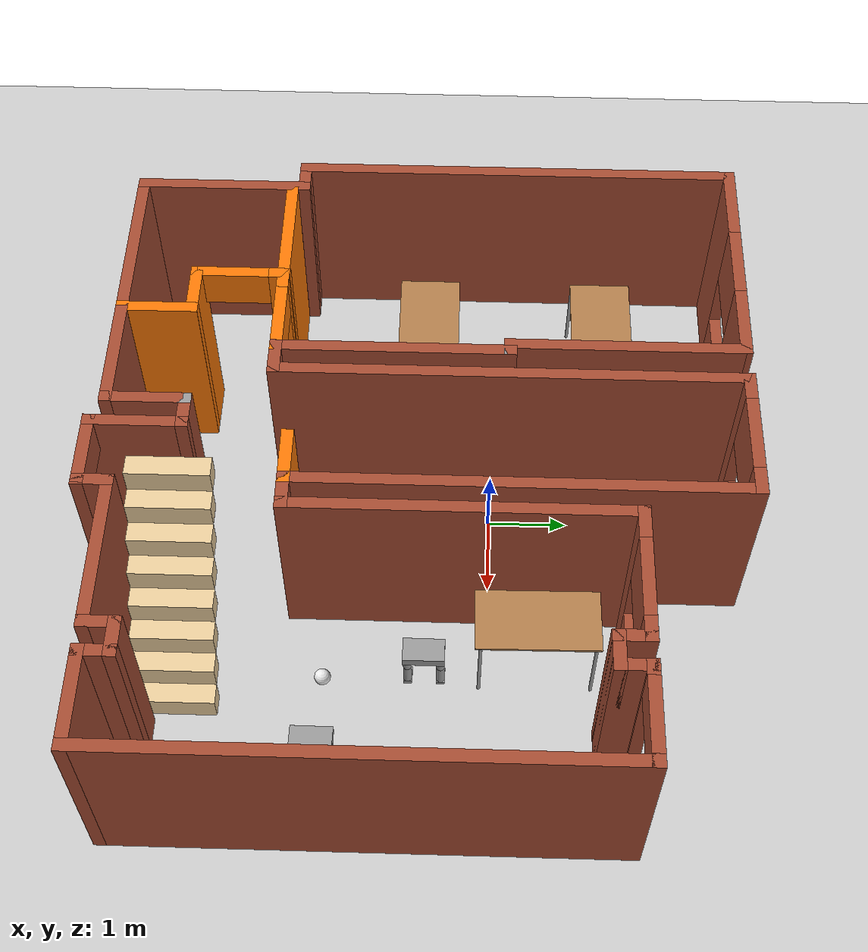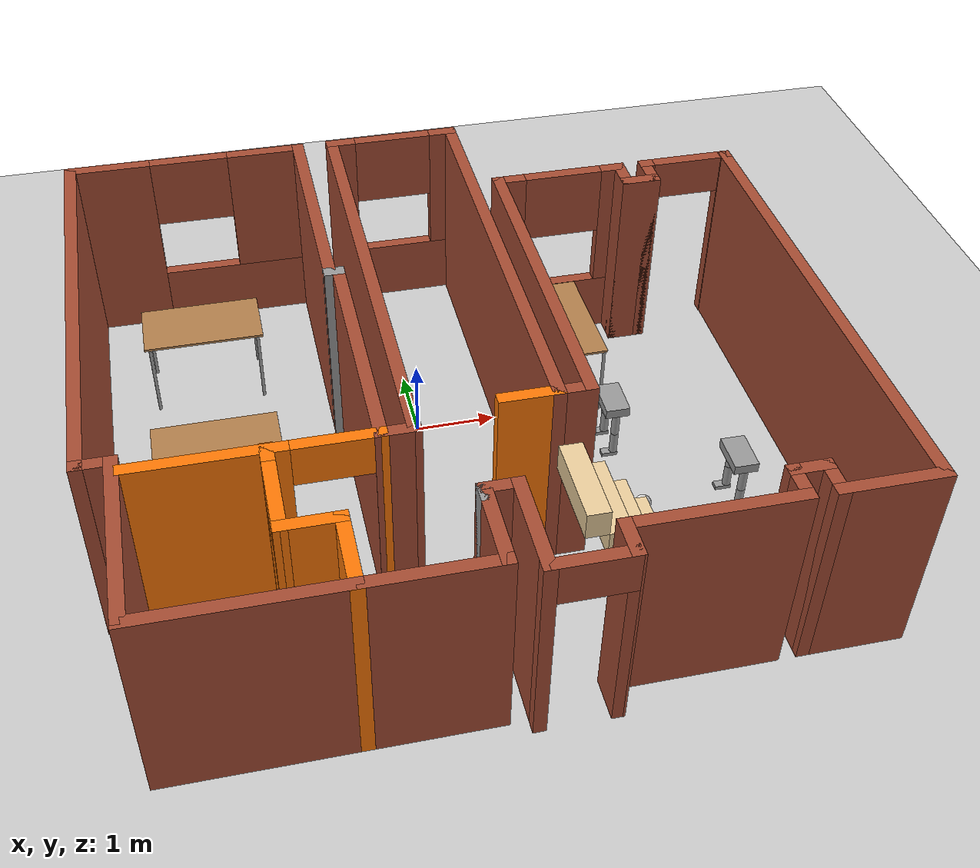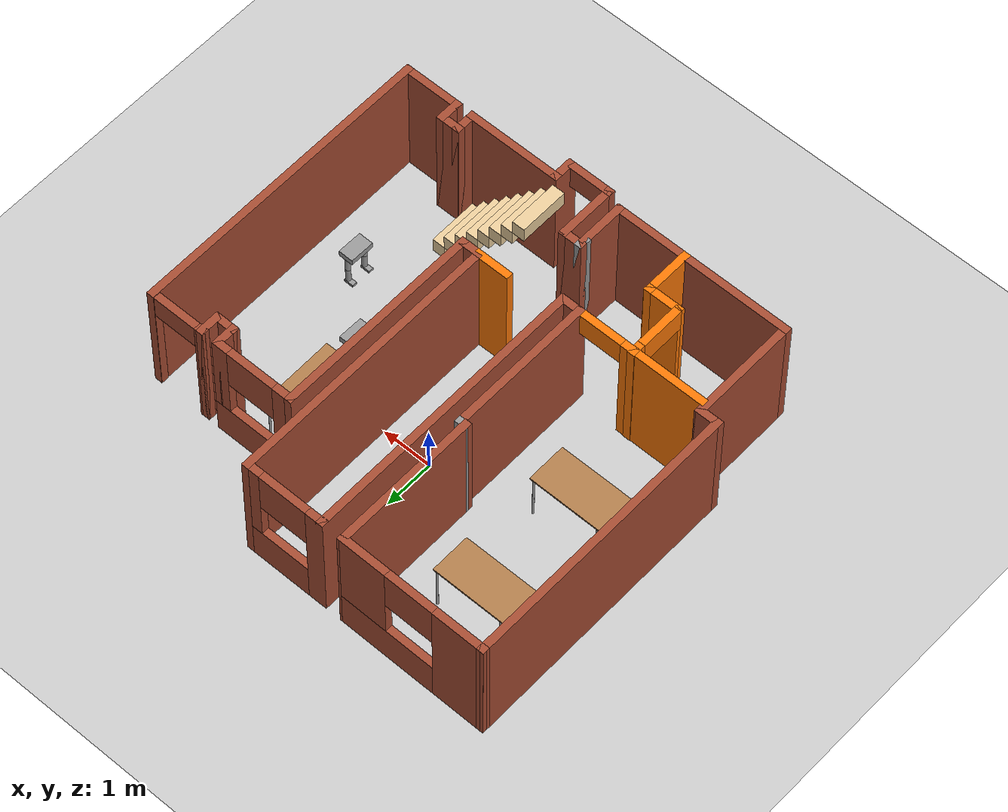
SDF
<sdf version="1.6">
 <world name="default">
  <plugin name="hello" filename="libhello.so"/>
  <light name="sun" type="directional">
   <pose>0 0 10 0 -0 0</pose>
   <diffuse>0.8 0.8 0.8 1</diffuse>
   <specular>0.2 0.2 0.2 1</specular>
   <attenuation>
    <range>1000</range>
    <constant>0.9</constant>
    <linear>0.01</linear>
    <quadratic>0.001</quadratic>
   </attenuation>
   <direction>-0.5 0.1 -0.9</direction>
  </light>
  <model name="ground_plane">
   <static>1</static>
   <link name="link">
    <collision name="collision">
     <geometry><plane><normal>0 0 1</normal><size>100 100</size></plane></geometry>
     <surface><friction><ode><mu>100</mu><mu2>50</mu2></ode></friction></surface>
    </collision>
    <visual name="visual">
     <cast_shadows>0</cast_shadows>
     <geometry><plane><normal>0 0 1</normal><size>100 100</size></plane></geometry>
     <material>
      <script><uri>file://media/materials/scripts/gazebo.material</uri><name>Gazebo/Grey</name></script>
     </material>
    </visual>
   </link>
  </model>
  <gravity>0 0 -9.8</gravity>
  <magnetic_field>6e-06 2.3e-05 -4.2e-05</magnetic_field>
  <atmosphere type="adiabatic"/>
  <physics name="default_physics" default="0" type="ode">
   <max_step_size>0.001</max_step_size>
   <real_time_factor>1</real_time_factor>
   <real_time_update_rate>1000</real_time_update_rate>
  </physics>
  <scene><ambient>0.4 0.4 0.4 1</ambient><background>0.7 0.7 0.7 1</background><shadows>1</shadows></scene>
  <spherical_coordinates>
   <surface_model>EARTH_WGS84</surface_model>
   <latitude_deg>0</latitude_deg>
   <longitude_deg>0</longitude_deg>
   <elevation>0</elevation>
   <heading_deg>0</heading_deg>
  </spherical_coordinates>
  <model name="table_4">
   <static>1</static>
   <link name="link">
    <collision name="surface">
     <pose>0 0 1 0 -0 0</pose>
     <geometry><box><size>1.5 0.8 0.03</size></box></geometry>
     <surface><friction><ode><mu>0.6</mu><mu2>0.6</mu2></ode></friction></surface>
    </collision>
    <visual name="visual1">
     <pose>0 0 1 0 -0 0</pose>
     <geometry><box><size>1.5 0.8 0.03</size></box></geometry>
     <material>
      <script><uri>file://media/materials/scripts/gazebo.material</uri><name>Gazebo/Wood</name></script>
     </material>
    </visual>
    <collision name="front_left_leg">
     <pose>0.68 0.38 0.5 0 -0 0</pose>
     <geometry><cylinder><radius>0.02</radius><length>1</length></cylinder></geometry>
    </collision>
    <visual name="front_left_leg">
     <pose>0.68 0.38 0.5 0 -0 0</pose>
     <geometry><cylinder><radius>0.02</radius><length>1</length></cylinder></geometry>
     <material>
      <script><uri>file://media/materials/scripts/gazebo.material</uri><name>Gazebo/Grey</name></script>
     </material>
    </visual>
    <collision name="front_right_leg">
     <pose>0.68 -0.38 0.5 0 -0 0</pose>
     <geometry><cylinder><radius>0.02</radius><length>1</length></cylinder></geometry>
    </collision>
    <visual name="front_right_leg">
     <pose>0.68 -0.38 0.5 0 -0 0</pose>
     <geometry><cylinder><radius>0.02</radius><length>1</length></cylinder></geometry>
     <material>
      <script><uri>file://media/materials/scripts/gazebo.material</uri><name>Gazebo/Grey</name></script>
     </material>
    </visual>
    <collision name="back_right_leg">
     <pose>-0.68 -0.38 0.5 0 -0 0</pose>
     <geometry><cylinder><radius>0.02</radius><length>1</length></cylinder></geometry>
    </collision>
    <visual name="back_right_leg">
     <pose>-0.68 -0.38 0.5 0 -0 0</pose>
     <geometry><cylinder><radius>0.02</radius><length>1</length></cylinder></geometry>
     <material>
      <script><uri>file://media/materials/scripts/gazebo.material</uri><name>Gazebo/Grey</name></script>
     </material>
    </visual>
    <collision name="back_left_leg">
     <pose>-0.68 0.38 0.5 0 -0 0</pose>
     <geometry><cylinder><radius>0.02</radius><length>1</length></cylinder></geometry>
    </collision>
    <visual name="back_left_leg">
     <pose>-0.68 0.38 0.5 0 -0 0</pose>
     <geometry><cylinder><radius>0.02</radius><length>1</length></cylinder></geometry>
     <material>
      <script><uri>file://media/materials/scripts/gazebo.material</uri><name>Gazebo/Grey</name></script>
     </material>
    </visual>
   </link>
   <pose>-2.54391 -0.8404 0 0 -0 0</pose>
  </model>
  <model name="table_5">
   <static>1</static>
   <link name="link">
    <collision name="surface">
     <pose>0 0 1 0 -0 0</pose>
     <geometry><box><size>1.5 0.8 0.03</size></box></geometry>
     <surface><friction><ode><mu>0.6</mu><mu2>0.6</mu2></ode></friction></surface>
    </collision>
    <visual name="visual1">
     <pose>0 0 1 0 -0 0</pose>
     <geometry><box><size>1.5 0.8 0.03</size></box></geometry>
     <material>
      <script><uri>file://media/materials/scripts/gazebo.material</uri><name>Gazebo/Wood</name></script>
     </material>
    </visual>
    <collision name="front_left_leg">
     <pose>0.68 0.38 0.5 0 -0 0</pose>
     <geometry><cylinder><radius>0.02</radius><length>1</length></cylinder></geometry>
    </collision>
    <visual name="front_left_leg">
     <pose>0.68 0.38 0.5 0 -0 0</pose>
     <geometry><cylinder><radius>0.02</radius><length>1</length></cylinder></geometry>
     <material>
      <script><uri>file://media/materials/scripts/gazebo.material</uri><name>Gazebo/Grey</name></script>
     </material>
    </visual>
    <collision name="front_right_leg">
     <pose>0.68 -0.38 0.5 0 -0 0</pose>
     <geometry><cylinder><radius>0.02</radius><length>1</length></cylinder></geometry>
    </collision>
    <visual name="front_right_leg">
     <pose>0.68 -0.38 0.5 0 -0 0</pose>
     <geometry><cylinder><radius>0.02</radius><length>1</length></cylinder></geometry>
     <material>
      <script><uri>file://media/materials/scripts/gazebo.material</uri><name>Gazebo/Grey</name></script>
     </material>
    </visual>
    <collision name="back_right_leg">
     <pose>-0.68 -0.38 0.5 0 -0 0</pose>
     <geometry><cylinder><radius>0.02</radius><length>1</length></cylinder></geometry>
    </collision>
    <visual name="back_right_leg">
     <pose>-0.68 -0.38 0.5 0 -0 0</pose>
     <geometry><cylinder><radius>0.02</radius><length>1</length></cylinder></geometry>
     <material>
      <script><uri>file://media/materials/scripts/gazebo.material</uri><name>Gazebo/Grey</name></script>
     </material>
    </visual>
    <collision name="back_left_leg">
     <pose>-0.68 0.38 0.5 0 -0 0</pose>
     <geometry><cylinder><radius>0.02</radius><length>1</length></cylinder></geometry>
    </collision>
    <visual name="back_left_leg">
     <pose>-0.68 0.38 0.5 0 -0 0</pose>
     <geometry><cylinder><radius>0.02</radius><length>1</length></cylinder></geometry>
     <material>
      <script><uri>file://media/materials/scripts/gazebo.material</uri><name>Gazebo/Grey</name></script>
     </material>
    </visual>
   </link>
   <pose>2.01572 0.578498 0 0 0 -1.56109</pose>
  </model>
  <model name="Humanoid">
   <link name="link_0">
    <pose>0.336877 -1.8722 0.949715 -0 -0 -0</pose>
    <inertial>
     <mass>1</mass>
     <inertia>
      <ixx>0.166667</ixx>
      <ixy>0</ixy>
      <ixz>0</ixz>
      <iyy>0.166667</iyy>
      <iyz>0</iyz>
      <izz>0.166667</izz>
     </inertia>
    </inertial>
    <visual name="visual">
     <geometry><box><size>0.3 0.5 0.12</size></box></geometry>
     <material>
      <lighting>1</lighting>
      <script><uri>file://media/materials/scripts/gazebo.material</uri><name>Gazebo/Grey</name></script>
      <shader type="pixel"><normal_map>__default__</normal_map></shader>
      <ambient>0.3 0.3 0.3 1</ambient>
      <diffuse>0.7 0.7 0.7 1</diffuse>
      <specular>0.01 0.01 0.01 1</specular>
      <emissive>0 0 0 1</emissive>
     </material>
    </visual>
    <collision name="collision">
     <geometry><box><size>0.3 0.5 0.1</size></box></geometry>
     <surface>
      <friction>
       <ode><mu>1</mu><mu2>1</mu2><fdir1>0 0 0</fdir1><slip1>0</slip1><slip2>0</slip2></ode>
       <torsional>
        <coefficient>1</coefficient>
        <patch_radius>0</patch_radius>
        <surface_radius>0</surface_radius>
        <use_patch_radius>1</use_patch_radius>
        <ode><slip>0</slip></ode>
       </torsional>
      </friction>
      <bounce><restitution_coefficient>0</restitution_coefficient><threshold>1e+06</threshold></bounce>
      <contact>
       <collide_without_contact>0</collide_without_contact>
       <collide_without_contact_bitmask>1</collide_without_contact_bitmask>
       <collide_bitmask>1</collide_bitmask>
       <ode>
        <soft_cfm>0</soft_cfm>
        <soft_erp>0.2</soft_erp>
        <kp>1e+13</kp>
        <kd>1</kd>
        <max_vel>0.01</max_vel>
        <min_depth>0</min_depth>
       </ode>
       <bullet>
        <split_impulse>1</split_impulse>
        <split_impulse_penetration_threshold>-0.01</split_impulse_penetration_threshold>
        <soft_cfm>0</soft_cfm>
        <soft_erp>0.2</soft_erp>
        <kp>1e+13</kp>
        <kd>1</kd>
       </bullet>
      </contact>
     </surface>
    </collision>
   </link>
   <link name="link_1">
    <pose>0.33738 -2.07145 0.439715 -0 -0 -0</pose>
    <inertial>
     <mass>1</mass>
     <inertia><ixx>0.145833</ixx><ixy>0</ixy><ixz>0</ixz><iyy>0.145833</iyy><iyz>0</iyz><izz>0.125</izz></inertia>
    </inertial>
    <visual name="visual">
     <geometry><cylinder><radius>0.05</radius><length>0.3</length></cylinder></geometry>
     <material>
      <lighting>1</lighting>
      <script><uri>file://media/materials/scripts/gazebo.material</uri><name>Gazebo/Grey</name></script>
      <shader type="pixel"><normal_map>__default__</normal_map></shader>
      <ambient>0.3 0.3 0.3 1</ambient>
      <diffuse>0.7 0.7 0.7 1</diffuse>
      <specular>0.01 0.01 0.01 1</specular>
      <emissive>0 0 0 1</emissive>
     </material>
    </visual>
    <collision name="collision">
     <geometry><cylinder><radius>0.05</radius><length>0.3</length></cylinder></geometry>
     <surface>
      <friction>
       <ode><mu>1</mu><mu2>1</mu2><fdir1>0 0 0</fdir1><slip1>0</slip1><slip2>0</slip2></ode>
       <torsional>
        <coefficient>1</coefficient>
        <patch_radius>0</patch_radius>
        <surface_radius>0</surface_radius>
        <use_patch_radius>1</use_patch_radius>
        <ode><slip>0</slip></ode>
       </torsional>
      </friction>
      <bounce><restitution_coefficient>0</restitution_coefficient><threshold>1e+06</threshold></bounce>
      <contact>
       <collide_without_contact>0</collide_without_contact>
       <collide_without_contact_bitmask>1</collide_without_contact_bitmask>
       <collide_bitmask>1</collide_bitmask>
       <ode>
        <soft_cfm>0</soft_cfm>
        <soft_erp>0.2</soft_erp>
        <kp>1e+13</kp>
        <kd>1</kd>
        <max_vel>0.01</max_vel>
        <min_depth>0</min_depth>
       </ode>
       <bullet>
        <split_impulse>1</split_impulse>
        <split_impulse_penetration_threshold>-0.01</split_impulse_penetration_threshold>
        <soft_cfm>0</soft_cfm>
        <soft_erp>0.2</soft_erp>
        <kp>1e+13</kp>
        <kd>1</kd>
       </bullet>
      </contact>
     </surface>
    </collision>
   </link>
   <link name="link_1_clone">
    <pose>0.336877 -2.0722 0.739716 -0 -0 -0</pose>
    <inertial>
     <mass>1</mass>
     <inertia><ixx>0.145833</ixx><ixy>0</ixy><ixz>0</ixz><iyy>0.145833</iyy><iyz>0</iyz><izz>0.125</izz></inertia>
    </inertial>
    <visual name="visual">
     <geometry><cylinder><radius>0.05</radius><length>0.3</length></cylinder></geometry>
     <material>
      <lighting>1</lighting>
      <script><uri>file://media/materials/scripts/gazebo.material</uri><name>Gazebo/Grey</name></script>
      <shader type="pixel"><normal_map>__default__</normal_map></shader>
      <ambient>0.3 0.3 0.3 1</ambient>
      <diffuse>0.7 0.7 0.7 1</diffuse>
      <specular>0.01 0.01 0.01 1</specular>
      <emissive>0 0 0 1</emissive>
     </material>
    </visual>
    <collision name="collision">
     <geometry><cylinder><radius>0.05</radius><length>0.3</length></cylinder></geometry>
     <surface>
      <friction>
       <ode><mu>1</mu><mu2>1</mu2><fdir1>0 0 0</fdir1><slip1>0</slip1><slip2>0</slip2></ode>
       <torsional>
        <coefficient>1</coefficient>
        <patch_radius>0</patch_radius>
        <surface_radius>0</surface_radius>
        <use_patch_radius>1</use_patch_radius>
        <ode><slip>0</slip></ode>
       </torsional>
      </friction>
      <bounce><restitution_coefficient>0</restitution_coefficient><threshold>1e+06</threshold></bounce>
      <contact>
       <collide_without_contact>0</collide_without_contact>
       <collide_without_contact_bitmask>1</collide_without_contact_bitmask>
       <collide_bitmask>1</collide_bitmask>
       <ode>
        <soft_cfm>0</soft_cfm>
        <soft_erp>0.2</soft_erp>
        <kp>1e+13</kp>
        <kd>1</kd>
        <max_vel>0.01</max_vel>
        <min_depth>0</min_depth>
       </ode>
       <bullet>
        <split_impulse>1</split_impulse>
        <split_impulse_penetration_threshold>-0.01</split_impulse_penetration_threshold>
        <soft_cfm>0</soft_cfm>
        <soft_erp>0.2</soft_erp>
        <kp>1e+13</kp>
        <kd>1</kd>
       </bullet>
      </contact>
     </surface>
    </collision>
   </link>
   <link name="link_1_clone_0">
    <pose>0.336877 -1.6722 0.739716 -0 -0 -0</pose>
    <inertial>
     <mass>1</mass>
     <inertia><ixx>0.145833</ixx><ixy>0</ixy><ixz>0</ixz><iyy>0.145833</iyy><iyz>0</iyz><izz>0.125</izz></inertia>
    </inertial>
    <visual name="visual">
     <geometry><cylinder><radius>0.05</radius><length>0.3</length></cylinder></geometry>
     <material>
      <lighting>1</lighting>
      <script><uri>file://media/materials/scripts/gazebo.material</uri><name>Gazebo/Grey</name></script>
      <shader type="pixel"><normal_map>__default__</normal_map></shader>
      <ambient>0.3 0.3 0.3 1</ambient>
      <diffuse>0.7 0.7 0.7 1</diffuse>
      <specular>0.01 0.01 0.01 1</specular>
      <emissive>0 0 0 1</emissive>
     </material>
    </visual>
    <collision name="collision">
     <geometry><cylinder><radius>0.05</radius><length>0.3</length></cylinder></geometry>
     <surface>
      <friction>
       <ode><mu>1</mu><mu2>1</mu2><fdir1>0 0 0</fdir1><slip1>0</slip1><slip2>0</slip2></ode>
       <torsional>
        <coefficient>1</coefficient>
        <patch_radius>0</patch_radius>
        <surface_radius>0</surface_radius>
        <use_patch_radius>1</use_patch_radius>
        <ode><slip>0</slip></ode>
       </torsional>
      </friction>
      <bounce><restitution_coefficient>0</restitution_coefficient><threshold>1e+06</threshold></bounce>
      <contact>
       <collide_without_contact>0</collide_without_contact>
       <collide_without_contact_bitmask>1</collide_without_contact_bitmask>
       <collide_bitmask>1</collide_bitmask>
       <ode>
        <soft_cfm>0</soft_cfm>
        <soft_erp>0.2</soft_erp>
        <kp>1e+13</kp>
        <kd>1</kd>
        <max_vel>0.01</max_vel>
        <min_depth>0</min_depth>
       </ode>
       <bullet>
        <split_impulse>1</split_impulse>
        <split_impulse_penetration_threshold>-0.01</split_impulse_penetration_threshold>
        <soft_cfm>0</soft_cfm>
        <soft_erp>0.2</soft_erp>
        <kp>1e+13</kp>
        <kd>1</kd>
       </bullet>
      </contact>
     </surface>
    </collision>
   </link>
   <link name="link_1_clone_1">
    <pose>0.336877 -1.6722 0.439715 -0 -0 -0</pose>
    <inertial>
     <mass>1</mass>
     <inertia><ixx>0.145833</ixx><ixy>0</ixy><ixz>0</ixz><iyy>0.145833</iyy><iyz>0</iyz><izz>0.125</izz></inertia>
    </inertial>
    <visual name="visual">
     <geometry><cylinder><radius>0.05</radius><length>0.3</length></cylinder></geometry>
     <material>
      <lighting>1</lighting>
      <script><uri>file://media/materials/scripts/gazebo.material</uri><name>Gazebo/Grey</name></script>
      <shader type="pixel"><normal_map>__default__</normal_map></shader>
      <ambient>0.3 0.3 0.3 1</ambient>
      <diffuse>0.7 0.7 0.7 1</diffuse>
      <specular>0.01 0.01 0.01 1</specular>
      <emissive>0 0 0 1</emissive>
     </material>
    </visual>
    <collision name="collision">
     <geometry><cylinder><radius>0.05</radius><length>0.3</length></cylinder></geometry>
     <surface>
      <friction>
       <ode><mu>1</mu><mu2>1</mu2><fdir1>0 0 0</fdir1><slip1>0</slip1><slip2>0</slip2></ode>
       <torsional>
        <coefficient>1</coefficient>
        <patch_radius>0</patch_radius>
        <surface_radius>0</surface_radius>
        <use_patch_radius>1</use_patch_radius>
        <ode><slip>0</slip></ode>
       </torsional>
      </friction>
      <bounce><restitution_coefficient>0</restitution_coefficient><threshold>1e+06</threshold></bounce>
      <contact>
       <collide_without_contact>0</collide_without_contact>
       <collide_without_contact_bitmask>1</collide_without_contact_bitmask>
       <collide_bitmask>1</collide_bitmask>
       <ode>
        <soft_cfm>0</soft_cfm>
        <soft_erp>0.2</soft_erp>
        <kp>1e+13</kp>
        <kd>1</kd>
        <max_vel>0.01</max_vel>
        <min_depth>0</min_depth>
       </ode>
       <bullet>
        <split_impulse>1</split_impulse>
        <split_impulse_penetration_threshold>-0.01</split_impulse_penetration_threshold>
        <soft_cfm>0</soft_cfm>
        <soft_erp>0.2</soft_erp>
        <kp>1e+13</kp>
        <kd>1</kd>
       </bullet>
      </contact>
     </surface>
    </collision>
   </link>
   <link name="link_2">
    <pose>0.284566 -2.06785 0.266379 -0 -0 -0</pose>
    <inertial>
     <mass>1</mass>
     <inertia>
      <ixx>0.166667</ixx>
      <ixy>0</ixy>
      <ixz>0</ixz>
      <iyy>0.166667</iyy>
      <iyz>0</iyz>
      <izz>0.166667</izz>
     </inertia>
    </inertial>
    <visual name="visual">
     <geometry><box><size>0.2 0.1 0.05</size></box></geometry>
     <material>
      <lighting>1</lighting>
      <script><uri>file://media/materials/scripts/gazebo.material</uri><name>Gazebo/Grey</name></script>
      <shader type="pixel"><normal_map>__default__</normal_map></shader>
      <ambient>0.3 0.3 0.3 1</ambient>
      <diffuse>0.7 0.7 0.7 1</diffuse>
      <specular>0.01 0.01 0.01 1</specular>
      <emissive>0 0 0 1</emissive>
     </material>
    </visual>
    <collision name="collision">
     <geometry><box><size>0.2 0.1 0.05</size></box></geometry>
     <surface>
      <friction>
       <ode><mu>1</mu><mu2>1</mu2><fdir1>0 0 0</fdir1><slip1>0</slip1><slip2>0</slip2></ode>
       <torsional>
        <coefficient>1</coefficient>
        <patch_radius>0</patch_radius>
        <surface_radius>0</surface_radius>
        <use_patch_radius>1</use_patch_radius>
        <ode><slip>0</slip></ode>
       </torsional>
      </friction>
      <bounce><restitution_coefficient>0</restitution_coefficient><threshold>1e+06</threshold></bounce>
      <contact>
       <collide_without_contact>0</collide_without_contact>
       <collide_without_contact_bitmask>1</collide_without_contact_bitmask>
       <collide_bitmask>1</collide_bitmask>
       <ode>
        <soft_cfm>0</soft_cfm>
        <soft_erp>0.2</soft_erp>
        <kp>1e+13</kp>
        <kd>1</kd>
        <max_vel>0.01</max_vel>
        <min_depth>0</min_depth>
       </ode>
       <bullet>
        <split_impulse>1</split_impulse>
        <split_impulse_penetration_threshold>-0.01</split_impulse_penetration_threshold>
        <soft_cfm>0</soft_cfm>
        <soft_erp>0.2</soft_erp>
        <kp>1e+13</kp>
        <kd>1</kd>
       </bullet>
      </contact>
     </surface>
    </collision>
   </link>
   <link name="link_2_clone">
    <pose>0.284446 -1.67061 0.264715 -0 -0 -0</pose>
    <inertial>
     <mass>1</mass>
     <inertia>
      <ixx>0.166667</ixx>
      <ixy>0</ixy>
      <ixz>0</ixz>
      <iyy>0.166667</iyy>
      <iyz>0</iyz>
      <izz>0.166667</izz>
     </inertia>
    </inertial>
    <visual name="visual">
     <geometry><box><size>0.2 0.1 0.05</size></box></geometry>
     <material>
      <lighting>1</lighting>
      <script><uri>file://media/materials/scripts/gazebo.material</uri><name>Gazebo/Grey</name></script>
      <shader type="pixel"><normal_map>__default__</normal_map></shader>
      <ambient>0.3 0.3 0.3 1</ambient>
      <diffuse>0.7 0.7 0.7 1</diffuse>
      <specular>0.01 0.01 0.01 1</specular>
      <emissive>0 0 0 1</emissive>
     </material>
    </visual>
    <collision name="collision">
     <geometry><box><size>0.2 0.1 0.05</size></box></geometry>
     <surface>
      <friction>
       <ode><mu>1</mu><mu2>1</mu2><fdir1>0 0 0</fdir1><slip1>0</slip1><slip2>0</slip2></ode>
       <torsional>
        <coefficient>1</coefficient>
        <patch_radius>0</patch_radius>
        <surface_radius>0</surface_radius>
        <use_patch_radius>1</use_patch_radius>
        <ode><slip>0</slip></ode>
       </torsional>
      </friction>
      <bounce><restitution_coefficient>0</restitution_coefficient><threshold>1e+06</threshold></bounce>
      <contact>
       <collide_without_contact>0</collide_without_contact>
       <collide_without_contact_bitmask>1</collide_without_contact_bitmask>
       <collide_bitmask>1</collide_bitmask>
       <ode>
        <soft_cfm>0</soft_cfm>
        <soft_erp>0.2</soft_erp>
        <kp>1e+13</kp>
        <kd>1</kd>
        <max_vel>0.01</max_vel>
        <min_depth>0</min_depth>
       </ode>
       <bullet>
        <split_impulse>1</split_impulse>
        <split_impulse_penetration_threshold>-0.01</split_impulse_penetration_threshold>
        <soft_cfm>0</soft_cfm>
        <soft_erp>0.2</soft_erp>
        <kp>1e+13</kp>
        <kd>1</kd>
       </bullet>
      </contact>
     </surface>
    </collision>
   </link>
   <joint name="link_0_JOINT_0" type="fixed">
    <parent>link_0</parent>
    <child>link_1_clone</child>
    <physics>
     <ode><limit><cfm>0</cfm><erp>0.2</erp></limit><suspension><cfm>0</cfm><erp>0.2</erp></suspension></ode>
    </physics>
   </joint>
   <joint name="link_0_JOINT_1" type="fixed">
    <parent>link_0</parent>
    <child>link_1_clone_0</child>
    <physics>
     <ode><limit><cfm>0</cfm><erp>0.2</erp></limit><suspension><cfm>0</cfm><erp>0.2</erp></suspension></ode>
    </physics>
   </joint>
   <joint name="link_1_JOINT_5" type="fixed">
    <parent>link_1</parent>
    <child>link_2</child>
    <physics>
     <ode><limit><cfm>0</cfm><erp>0.2</erp></limit><suspension><cfm>0</cfm><erp>0.2</erp></suspension></ode>
    </physics>
   </joint>
   <joint name="link_1_clone_0_JOINT_2" type="fixed">
    <parent>link_1_clone_0</parent>
    <child>link_1_clone_1</child>
    <physics>
     <ode><limit><cfm>0</cfm><erp>0.2</erp></limit><suspension><cfm>0</cfm><erp>0.2</erp></suspension></ode>
    </physics>
   </joint>
   <joint name="link_1_clone_1_JOINT_4" type="fixed">
    <parent>link_1_clone_1</parent>
    <child>link_2_clone</child>
    <physics>
     <ode><limit><cfm>0</cfm><erp>0.2</erp></limit><suspension><cfm>0</cfm><erp>0.2</erp></suspension></ode>
    </physics>
   </joint>
   <joint name="link_1_clone_JOINT_3" type="revolute">
    <parent>link_1_clone</parent>
    <child>link_1</child>
    <axis>
     <xyz>1 0 0</xyz>
     <use_parent_model_frame>0</use_parent_model_frame>
     <limit>
      <lower>-1.79769e+308</lower>
      <upper>1.79769e+308</upper>
      <effort>-1</effort>
      <velocity>-1</velocity>
     </limit>
     <dynamics>
      <spring_reference>0</spring_reference>
      <spring_stiffness>0</spring_stiffness>
      <damping>0</damping>
      <friction>0</friction>
     </dynamics>
    </axis>
    <physics>
     <ode><limit><cfm>0</cfm><erp>0.2</erp></limit><suspension><cfm>0</cfm><erp>0.2</erp></suspension></ode>
    </physics>
   </joint>
   <static>0</static>
   <pose>3.18747 -0.142987 -0.231577 0.00473 -4e-06 -0.012782</pose>
  </model>
  <model name="Humanoid_0">
   <link name="link_0">
    <pose>0.336877 -1.8722 0.949715 -0 -0 -0</pose>
    <inertial>
     <mass>1</mass>
     <inertia>
      <ixx>0.166667</ixx>
      <ixy>0</ixy>
      <ixz>0</ixz>
      <iyy>0.166667</iyy>
      <iyz>0</iyz>
      <izz>0.166667</izz>
     </inertia>
    </inertial>
    <visual name="visual">
     <geometry><box><size>0.3 0.5 0.12</size></box></geometry>
     <material>
      <lighting>1</lighting>
      <script><uri>file://media/materials/scripts/gazebo.material</uri><name>Gazebo/Grey</name></script>
      <shader type="pixel"><normal_map>__default__</normal_map></shader>
      <ambient>0.3 0.3 0.3 1</ambient>
      <diffuse>0.7 0.7 0.7 1</diffuse>
      <specular>0.01 0.01 0.01 1</specular>
      <emissive>0 0 0 1</emissive>
     </material>
    </visual>
    <collision name="collision">
     <geometry><box><size>0.3 0.5 0.1</size></box></geometry>
     <surface>
      <friction>
       <ode><mu>1</mu><mu2>1</mu2><fdir1>0 0 0</fdir1><slip1>0</slip1><slip2>0</slip2></ode>
       <torsional>
        <coefficient>1</coefficient>
        <patch_radius>0</patch_radius>
        <surface_radius>0</surface_radius>
        <use_patch_radius>1</use_patch_radius>
        <ode><slip>0</slip></ode>
       </torsional>
      </friction>
      <bounce><restitution_coefficient>0</restitution_coefficient><threshold>1e+06</threshold></bounce>
      <contact>
       <collide_without_contact>0</collide_without_contact>
       <collide_without_contact_bitmask>1</collide_without_contact_bitmask>
       <collide_bitmask>1</collide_bitmask>
       <ode>
        <soft_cfm>0</soft_cfm>
        <soft_erp>0.2</soft_erp>
        <kp>1e+13</kp>
        <kd>1</kd>
        <max_vel>0.01</max_vel>
        <min_depth>0</min_depth>
       </ode>
       <bullet>
        <split_impulse>1</split_impulse>
        <split_impulse_penetration_threshold>-0.01</split_impulse_penetration_threshold>
        <soft_cfm>0</soft_cfm>
        <soft_erp>0.2</soft_erp>
        <kp>1e+13</kp>
        <kd>1</kd>
       </bullet>
      </contact>
     </surface>
    </collision>
   </link>
   <link name="link_1">
    <pose>0.33738 -2.07145 0.439715 -0 -0 -0</pose>
    <inertial>
     <mass>1</mass>
     <inertia><ixx>0.145833</ixx><ixy>0</ixy><ixz>0</ixz><iyy>0.145833</iyy><iyz>0</iyz><izz>0.125</izz></inertia>
    </inertial>
    <visual name="visual">
     <geometry><cylinder><radius>0.05</radius><length>0.3</length></cylinder></geometry>
     <material>
      <lighting>1</lighting>
      <script><uri>file://media/materials/scripts/gazebo.material</uri><name>Gazebo/Grey</name></script>
      <shader type="pixel"><normal_map>__default__</normal_map></shader>
      <ambient>0.3 0.3 0.3 1</ambient>
      <diffuse>0.7 0.7 0.7 1</diffuse>
      <specular>0.01 0.01 0.01 1</specular>
      <emissive>0 0 0 1</emissive>
     </material>
    </visual>
    <collision name="collision">
     <geometry><cylinder><radius>0.05</radius><length>0.3</length></cylinder></geometry>
     <surface>
      <friction>
       <ode><mu>1</mu><mu2>1</mu2><fdir1>0 0 0</fdir1><slip1>0</slip1><slip2>0</slip2></ode>
       <torsional>
        <coefficient>1</coefficient>
        <patch_radius>0</patch_radius>
        <surface_radius>0</surface_radius>
        <use_patch_radius>1</use_patch_radius>
        <ode><slip>0</slip></ode>
       </torsional>
      </friction>
      <bounce><restitution_coefficient>0</restitution_coefficient><threshold>1e+06</threshold></bounce>
      <contact>
       <collide_without_contact>0</collide_without_contact>
       <collide_without_contact_bitmask>1</collide_without_contact_bitmask>
       <collide_bitmask>1</collide_bitmask>
       <ode>
        <soft_cfm>0</soft_cfm>
        <soft_erp>0.2</soft_erp>
        <kp>1e+13</kp>
        <kd>1</kd>
        <max_vel>0.01</max_vel>
        <min_depth>0</min_depth>
       </ode>
       <bullet>
        <split_impulse>1</split_impulse>
        <split_impulse_penetration_threshold>-0.01</split_impulse_penetration_threshold>
        <soft_cfm>0</soft_cfm>
        <soft_erp>0.2</soft_erp>
        <kp>1e+13</kp>
        <kd>1</kd>
       </bullet>
      </contact>
     </surface>
    </collision>
   </link>
   <link name="link_1_clone">
    <pose>0.336877 -2.0722 0.739716 -0 -0 -0</pose>
    <inertial>
     <mass>1</mass>
     <inertia><ixx>0.145833</ixx><ixy>0</ixy><ixz>0</ixz><iyy>0.145833</iyy><iyz>0</iyz><izz>0.125</izz></inertia>
    </inertial>
    <visual name="visual">
     <geometry><cylinder><radius>0.05</radius><length>0.3</length></cylinder></geometry>
     <material>
      <lighting>1</lighting>
      <script><uri>file://media/materials/scripts/gazebo.material</uri><name>Gazebo/Grey</name></script>
      <shader type="pixel"><normal_map>__default__</normal_map></shader>
      <ambient>0.3 0.3 0.3 1</ambient>
      <diffuse>0.7 0.7 0.7 1</diffuse>
      <specular>0.01 0.01 0.01 1</specular>
      <emissive>0 0 0 1</emissive>
     </material>
    </visual>
    <collision name="collision">
     <geometry><cylinder><radius>0.05</radius><length>0.3</length></cylinder></geometry>
     <surface>
      <friction>
       <ode><mu>1</mu><mu2>1</mu2><fdir1>0 0 0</fdir1><slip1>0</slip1><slip2>0</slip2></ode>
       <torsional>
        <coefficient>1</coefficient>
        <patch_radius>0</patch_radius>
        <surface_radius>0</surface_radius>
        <use_patch_radius>1</use_patch_radius>
        <ode><slip>0</slip></ode>
       </torsional>
      </friction>
      <bounce><restitution_coefficient>0</restitution_coefficient><threshold>1e+06</threshold></bounce>
      <contact>
       <collide_without_contact>0</collide_without_contact>
       <collide_without_contact_bitmask>1</collide_without_contact_bitmask>
       <collide_bitmask>1</collide_bitmask>
       <ode>
        <soft_cfm>0</soft_cfm>
        <soft_erp>0.2</soft_erp>
        <kp>1e+13</kp>
        <kd>1</kd>
        <max_vel>0.01</max_vel>
        <min_depth>0</min_depth>
       </ode>
       <bullet>
        <split_impulse>1</split_impulse>
        <split_impulse_penetration_threshold>-0.01</split_impulse_penetration_threshold>
        <soft_cfm>0</soft_cfm>
        <soft_erp>0.2</soft_erp>
        <kp>1e+13</kp>
        <kd>1</kd>
       </bullet>
      </contact>
     </surface>
    </collision>
   </link>
   <link name="link_1_clone_0">
    <pose>0.336877 -1.6722 0.739716 -0 -0 -0</pose>
    <inertial>
     <mass>1</mass>
     <inertia><ixx>0.145833</ixx><ixy>0</ixy><ixz>0</ixz><iyy>0.145833</iyy><iyz>0</iyz><izz>0.125</izz></inertia>
    </inertial>
    <visual name="visual">
     <geometry><cylinder><radius>0.05</radius><length>0.3</length></cylinder></geometry>
     <material>
      <lighting>1</lighting>
      <script><uri>file://media/materials/scripts/gazebo.material</uri><name>Gazebo/Grey</name></script>
      <shader type="pixel"><normal_map>__default__</normal_map></shader>
      <ambient>0.3 0.3 0.3 1</ambient>
      <diffuse>0.7 0.7 0.7 1</diffuse>
      <specular>0.01 0.01 0.01 1</specular>
      <emissive>0 0 0 1</emissive>
     </material>
    </visual>
    <collision name="collision">
     <geometry><cylinder><radius>0.05</radius><length>0.3</length></cylinder></geometry>
     <surface>
      <friction>
       <ode><mu>1</mu><mu2>1</mu2><fdir1>0 0 0</fdir1><slip1>0</slip1><slip2>0</slip2></ode>
       <torsional>
        <coefficient>1</coefficient>
        <patch_radius>0</patch_radius>
        <surface_radius>0</surface_radius>
        <use_patch_radius>1</use_patch_radius>
        <ode><slip>0</slip></ode>
       </torsional>
      </friction>
      <bounce><restitution_coefficient>0</restitution_coefficient><threshold>1e+06</threshold></bounce>
      <contact>
       <collide_without_contact>0</collide_without_contact>
       <collide_without_contact_bitmask>1</collide_without_contact_bitmask>
       <collide_bitmask>1</collide_bitmask>
       <ode>
        <soft_cfm>0</soft_cfm>
        <soft_erp>0.2</soft_erp>
        <kp>1e+13</kp>
        <kd>1</kd>
        <max_vel>0.01</max_vel>
        <min_depth>0</min_depth>
       </ode>
       <bullet>
        <split_impulse>1</split_impulse>
        <split_impulse_penetration_threshold>-0.01</split_impulse_penetration_threshold>
        <soft_cfm>0</soft_cfm>
        <soft_erp>0.2</soft_erp>
        <kp>1e+13</kp>
        <kd>1</kd>
       </bullet>
      </contact>
     </surface>
    </collision>
   </link>
   <link name="link_1_clone_1">
    <pose>0.336877 -1.6722 0.439715 -0 -0 -0</pose>
    <inertial>
     <mass>1</mass>
     <inertia><ixx>0.145833</ixx><ixy>0</ixy><ixz>0</ixz><iyy>0.145833</iyy><iyz>0</iyz><izz>0.125</izz></inertia>
    </inertial>
    <visual name="visual">
     <geometry><cylinder><radius>0.05</radius><length>0.3</length></cylinder></geometry>
     <material>
      <lighting>1</lighting>
      <script><uri>file://media/materials/scripts/gazebo.material</uri><name>Gazebo/Grey</name></script>
      <shader type="pixel"><normal_map>__default__</normal_map></shader>
      <ambient>0.3 0.3 0.3 1</ambient>
      <diffuse>0.7 0.7 0.7 1</diffuse>
      <specular>0.01 0.01 0.01 1</specular>
      <emissive>0 0 0 1</emissive>
     </material>
    </visual>
    <collision name="collision">
     <geometry><cylinder><radius>0.05</radius><length>0.3</length></cylinder></geometry>
     <surface>
      <friction>
       <ode><mu>1</mu><mu2>1</mu2><fdir1>0 0 0</fdir1><slip1>0</slip1><slip2>0</slip2></ode>
       <torsional>
        <coefficient>1</coefficient>
        <patch_radius>0</patch_radius>
        <surface_radius>0</surface_radius>
        <use_patch_radius>1</use_patch_radius>
        <ode><slip>0</slip></ode>
       </torsional>
      </friction>
      <bounce><restitution_coefficient>0</restitution_coefficient><threshold>1e+06</threshold></bounce>
      <contact>
       <collide_without_contact>0</collide_without_contact>
       <collide_without_contact_bitmask>1</collide_without_contact_bitmask>
       <collide_bitmask>1</collide_bitmask>
       <ode>
        <soft_cfm>0</soft_cfm>
        <soft_erp>0.2</soft_erp>
        <kp>1e+13</kp>
        <kd>1</kd>
        <max_vel>0.01</max_vel>
        <min_depth>0</min_depth>
       </ode>
       <bullet>
        <split_impulse>1</split_impulse>
        <split_impulse_penetration_threshold>-0.01</split_impulse_penetration_threshold>
        <soft_cfm>0</soft_cfm>
        <soft_erp>0.2</soft_erp>
        <kp>1e+13</kp>
        <kd>1</kd>
       </bullet>
      </contact>
     </surface>
    </collision>
   </link>
   <link name="link_2">
    <pose>0.284566 -2.06785 0.266379 -0 -0 -0</pose>
    <inertial>
     <mass>1</mass>
     <inertia>
      <ixx>0.166667</ixx>
      <ixy>0</ixy>
      <ixz>0</ixz>
      <iyy>0.166667</iyy>
      <iyz>0</iyz>
      <izz>0.166667</izz>
     </inertia>
    </inertial>
    <visual name="visual">
     <geometry><box><size>0.2 0.1 0.05</size></box></geometry>
     <material>
      <lighting>1</lighting>
      <script><uri>file://media/materials/scripts/gazebo.material</uri><name>Gazebo/Grey</name></script>
      <shader type="pixel"><normal_map>__default__</normal_map></shader>
      <ambient>0.3 0.3 0.3 1</ambient>
      <diffuse>0.7 0.7 0.7 1</diffuse>
      <specular>0.01 0.01 0.01 1</specular>
      <emissive>0 0 0 1</emissive>
     </material>
    </visual>
    <collision name="collision">
     <geometry><box><size>0.2 0.1 0.05</size></box></geometry>
     <surface>
      <friction>
       <ode><mu>1</mu><mu2>1</mu2><fdir1>0 0 0</fdir1><slip1>0</slip1><slip2>0</slip2></ode>
       <torsional>
        <coefficient>1</coefficient>
        <patch_radius>0</patch_radius>
        <surface_radius>0</surface_radius>
        <use_patch_radius>1</use_patch_radius>
        <ode><slip>0</slip></ode>
       </torsional>
      </friction>
      <bounce><restitution_coefficient>0</restitution_coefficient><threshold>1e+06</threshold></bounce>
      <contact>
       <collide_without_contact>0</collide_without_contact>
       <collide_without_contact_bitmask>1</collide_without_contact_bitmask>
       <collide_bitmask>1</collide_bitmask>
       <ode>
        <soft_cfm>0</soft_cfm>
        <soft_erp>0.2</soft_erp>
        <kp>1e+13</kp>
        <kd>1</kd>
        <max_vel>0.01</max_vel>
        <min_depth>0</min_depth>
       </ode>
       <bullet>
        <split_impulse>1</split_impulse>
        <split_impulse_penetration_threshold>-0.01</split_impulse_penetration_threshold>
        <soft_cfm>0</soft_cfm>
        <soft_erp>0.2</soft_erp>
        <kp>1e+13</kp>
        <kd>1</kd>
       </bullet>
      </contact>
     </surface>
    </collision>
   </link>
   <link name="link_2_clone">
    <pose>0.284446 -1.67061 0.264715 -0 -0 -0</pose>
    <inertial>
     <mass>1</mass>
     <inertia>
      <ixx>0.166667</ixx>
      <ixy>0</ixy>
      <ixz>0</ixz>
      <iyy>0.166667</iyy>
      <iyz>0</iyz>
      <izz>0.166667</izz>
     </inertia>
    </inertial>
    <visual name="visual">
     <geometry><box><size>0.2 0.1 0.05</size></box></geometry>
     <material>
      <lighting>1</lighting>
      <script><uri>file://media/materials/scripts/gazebo.material</uri><name>Gazebo/Grey</name></script>
      <shader type="pixel"><normal_map>__default__</normal_map></shader>
      <ambient>0.3 0.3 0.3 1</ambient>
      <diffuse>0.7 0.7 0.7 1</diffuse>
      <specular>0.01 0.01 0.01 1</specular>
      <emissive>0 0 0 1</emissive>
     </material>
    </visual>
    <collision name="collision">
     <geometry><box><size>0.2 0.1 0.05</size></box></geometry>
     <surface>
      <friction>
       <ode><mu>1</mu><mu2>1</mu2><fdir1>0 0 0</fdir1><slip1>0</slip1><slip2>0</slip2></ode>
       <torsional>
        <coefficient>1</coefficient>
        <patch_radius>0</patch_radius>
        <surface_radius>0</surface_radius>
        <use_patch_radius>1</use_patch_radius>
        <ode><slip>0</slip></ode>
       </torsional>
      </friction>
      <bounce><restitution_coefficient>0</restitution_coefficient><threshold>1e+06</threshold></bounce>
      <contact>
       <collide_without_contact>0</collide_without_contact>
       <collide_without_contact_bitmask>1</collide_without_contact_bitmask>
       <collide_bitmask>1</collide_bitmask>
       <ode>
        <soft_cfm>0</soft_cfm>
        <soft_erp>0.2</soft_erp>
        <kp>1e+13</kp>
        <kd>1</kd>
        <max_vel>0.01</max_vel>
        <min_depth>0</min_depth>
       </ode>
       <bullet>
        <split_impulse>1</split_impulse>
        <split_impulse_penetration_threshold>-0.01</split_impulse_penetration_threshold>
        <soft_cfm>0</soft_cfm>
        <soft_erp>0.2</soft_erp>
        <kp>1e+13</kp>
        <kd>1</kd>
       </bullet>
      </contact>
     </surface>
    </collision>
   </link>
   <joint name="link_0_JOINT_0" type="fixed">
    <parent>link_0</parent>
    <child>link_1_clone</child>
    <physics>
     <ode><limit><cfm>0</cfm><erp>0.2</erp></limit><suspension><cfm>0</cfm><erp>0.2</erp></suspension></ode>
    </physics>
   </joint>
   <joint name="link_0_JOINT_1" type="fixed">
    <parent>link_0</parent>
    <child>link_1_clone_0</child>
    <physics>
     <ode><limit><cfm>0</cfm><erp>0.2</erp></limit><suspension><cfm>0</cfm><erp>0.2</erp></suspension></ode>
    </physics>
   </joint>
   <joint name="link_1_JOINT_5" type="fixed">
    <parent>link_1</parent>
    <child>link_2</child>
    <physics>
     <ode><limit><cfm>0</cfm><erp>0.2</erp></limit><suspension><cfm>0</cfm><erp>0.2</erp></suspension></ode>
    </physics>
   </joint>
   <joint name="link_1_clone_0_JOINT_2" type="fixed">
    <parent>link_1_clone_0</parent>
    <child>link_1_clone_1</child>
    <physics>
     <ode><limit><cfm>0</cfm><erp>0.2</erp></limit><suspension><cfm>0</cfm><erp>0.2</erp></suspension></ode>
    </physics>
   </joint>
   <joint name="link_1_clone_1_JOINT_4" type="fixed">
    <parent>link_1_clone_1</parent>
    <child>link_2_clone</child>
    <physics>
     <ode><limit><cfm>0</cfm><erp>0.2</erp></limit><suspension><cfm>0</cfm><erp>0.2</erp></suspension></ode>
    </physics>
   </joint>
   <joint name="link_1_clone_JOINT_3" type="revolute">
    <parent>link_1_clone</parent>
    <child>link_1</child>
    <axis>
     <xyz>1 0 0</xyz>
     <use_parent_model_frame>0</use_parent_model_frame>
     <limit>
      <lower>-1.79769e+308</lower>
      <upper>1.79769e+308</upper>
      <effort>-1</effort>
      <velocity>-1</velocity>
     </limit>
     <dynamics>
      <spring_reference>0</spring_reference>
      <spring_stiffness>0</spring_stiffness>
      <damping>0</damping>
      <friction>0</friction>
     </dynamics>
    </axis>
    <physics>
     <ode><limit><cfm>0</cfm><erp>0.2</erp></limit><suspension><cfm>0</cfm><erp>0.2</erp></suspension></ode>
    </physics>
   </joint>
   <static>0</static>
   <pose>2.00455 1.11455 -0.231565 0.004737 4e-06 -0.012397</pose>
  </model>
  <audio><device>default</device></audio>
  <model name="Home">
   <link name="Stairs_2">
    <visual name="Stairs_2_Visual_0">
     <pose>2.4646 -2.89263 0.15625 0 0 -1.5708</pose>
     <geometry><box><size>1 0.25375 0.3125</size></box></geometry>
     <material>
      <script><uri>file://media/materials/scripts/gazebo.material</uri><name>Gazebo/Grey</name></script>
      <ambient>0.921569 0.807843 0.615686 1</ambient>
     </material>
     <meta><layer>0</layer></meta>
    </visual>
    <visual name="Stairs_2_Visual_1">
     <pose>2.21085 -2.89263 0.46875 0 0 -1.5708</pose>
     <geometry><box><size>1 0.25375 0.3125</size></box></geometry>
     <material>
      <script><uri>file://media/materials/scripts/gazebo.material</uri><name>Gazebo/Grey</name></script>
      <ambient>0.921569 0.807843 0.615686 1</ambient>
     </material>
     <meta><layer>0</layer></meta>
    </visual>
    <visual name="Stairs_2_Visual_2">
     <pose>1.9571 -2.89263 0.78125 0 0 -1.5708</pose>
     <geometry><box><size>1 0.25375 0.3125</size></box></geometry>
     <material>
      <script><uri>file://media/materials/scripts/gazebo.material</uri><name>Gazebo/Grey</name></script>
      <ambient>0.921569 0.807843 0.615686 1</ambient>
     </material>
     <meta><layer>0</layer></meta>
    </visual>
    <visual name="Stairs_2_Visual_3">
     <pose>1.70335 -2.89263 1.09375 0 0 -1.5708</pose>
     <geometry><box><size>1 0.25375 0.3125</size></box></geometry>
     <material>
      <script><uri>file://media/materials/scripts/gazebo.material</uri><name>Gazebo/Grey</name></script>
      <ambient>0.921569 0.807843 0.615686 1</ambient>
     </material>
     <meta><layer>0</layer></meta>
    </visual>
    <visual name="Stairs_2_Visual_4">
     <pose>1.4496 -2.89263 1.40625 0 0 -1.5708</pose>
     <geometry><box><size>1 0.25375 0.3125</size></box></geometry>
     <material>
      <script><uri>file://media/materials/scripts/gazebo.material</uri><name>Gazebo/Grey</name></script>
      <ambient>0.921569 0.807843 0.615686 1</ambient>
     </material>
     <meta><layer>0</layer></meta>
    </visual>
    <visual name="Stairs_2_Visual_5">
     <pose>1.19585 -2.89263 1.71875 0 0 -1.5708</pose>
     <geometry><box><size>1 0.25375 0.3125</size></box></geometry>
     <material>
      <script><uri>file://media/materials/scripts/gazebo.material</uri><name>Gazebo/Grey</name></script>
      <ambient>0.921569 0.807843 0.615686 1</ambient>
     </material>
     <meta><layer>0</layer></meta>
    </visual>
    <visual name="Stairs_2_Visual_6">
     <pose>0.942102 -2.89263 2.03125 0 0 -1.5708</pose>
     <geometry><box><size>1 0.25375 0.3125</size></box></geometry>
     <material>
      <script><uri>file://media/materials/scripts/gazebo.material</uri><name>Gazebo/Grey</name></script>
      <ambient>0.921569 0.807843 0.615686 1</ambient>
     </material>
     <meta><layer>0</layer></meta>
    </visual>
    <visual name="Stairs_2_Visual_7">
     <pose>0.688352 -2.89263 2.34375 0 0 -1.5708</pose>
     <geometry><box><size>1 0.25375 0.3125</size></box></geometry>
     <material>
      <script><uri>file://media/materials/scripts/gazebo.material</uri><name>Gazebo/Grey</name></script>
      <ambient>0.921569 0.807843 0.615686 1</ambient>
     </material>
     <meta><layer>0</layer></meta>
    </visual>
    <collision name="Stairs_2_Collision_0">
     <pose>2.4646 -2.89263 0.15625 0 0 -1.5708</pose>
     <geometry><box><size>1 0.25375 0.3125</size></box></geometry>
     <surface>
      <friction>
       <ode><mu>1</mu><mu2>1</mu2><fdir1>0 0 0</fdir1><slip1>0</slip1><slip2>0</slip2></ode>
       <torsional>
        <coefficient>1</coefficient>
        <patch_radius>0</patch_radius>
        <surface_radius>0</surface_radius>
        <use_patch_radius>1</use_patch_radius>
        <ode><slip>0</slip></ode>
       </torsional>
      </friction>
      <bounce><restitution_coefficient>0</restitution_coefficient><threshold>1e+06</threshold></bounce>
      <contact>
       <collide_without_contact>0</collide_without_contact>
       <collide_without_contact_bitmask>1</collide_without_contact_bitmask>
       <collide_bitmask>1</collide_bitmask>
       <ode>
        <soft_cfm>0</soft_cfm>
        <soft_erp>0.2</soft_erp>
        <kp>1e+13</kp>
        <kd>1</kd>
        <max_vel>0.01</max_vel>
        <min_depth>0</min_depth>
       </ode>
       <bullet>
        <split_impulse>1</split_impulse>
        <split_impulse_penetration_threshold>-0.01</split_impulse_penetration_threshold>
        <soft_cfm>0</soft_cfm>
        <soft_erp>0.2</soft_erp>
        <kp>1e+13</kp>
        <kd>1</kd>
       </bullet>
      </contact>
     </surface>
    </collision>
    <collision name="Stairs_2_Collision_1">
     <pose>2.21085 -2.89263 0.46875 0 0 -1.5708</pose>
     <geometry><box><size>1 0.25375 0.3125</size></box></geometry>
     <surface>
      <friction>
       <ode><mu>1</mu><mu2>1</mu2><fdir1>0 0 0</fdir1><slip1>0</slip1><slip2>0</slip2></ode>
       <torsional>
        <coefficient>1</coefficient>
        <patch_radius>0</patch_radius>
        <surface_radius>0</surface_radius>
        <use_patch_radius>1</use_patch_radius>
        <ode><slip>0</slip></ode>
       </torsional>
      </friction>
      <bounce><restitution_coefficient>0</restitution_coefficient><threshold>1e+06</threshold></bounce>
      <contact>
       <collide_without_contact>0</collide_without_contact>
       <collide_without_contact_bitmask>1</collide_without_contact_bitmask>
       <collide_bitmask>1</collide_bitmask>
       <ode>
        <soft_cfm>0</soft_cfm>
        <soft_erp>0.2</soft_erp>
        <kp>1e+13</kp>
        <kd>1</kd>
        <max_vel>0.01</max_vel>
        <min_depth>0</min_depth>
       </ode>
       <bullet>
        <split_impulse>1</split_impulse>
        <split_impulse_penetration_threshold>-0.01</split_impulse_penetration_threshold>
        <soft_cfm>0</soft_cfm>
        <soft_erp>0.2</soft_erp>
        <kp>1e+13</kp>
        <kd>1</kd>
       </bullet>
      </contact>
     </surface>
    </collision>
    <collision name="Stairs_2_Collision_2">
     <pose>1.9571 -2.89263 0.78125 0 0 -1.5708</pose>
     <geometry><box><size>1 0.25375 0.3125</size></box></geometry>
     <surface>
      <friction>
       <ode><mu>1</mu><mu2>1</mu2><fdir1>0 0 0</fdir1><slip1>0</slip1><slip2>0</slip2></ode>
       <torsional>
        <coefficient>1</coefficient>
        <patch_radius>0</patch_radius>
        <surface_radius>0</surface_radius>
        <use_patch_radius>1</use_patch_radius>
        <ode><slip>0</slip></ode>
       </torsional>
      </friction>
      <bounce><restitution_coefficient>0</restitution_coefficient><threshold>1e+06</threshold></bounce>
      <contact>
       <collide_without_contact>0</collide_without_contact>
       <collide_without_contact_bitmask>1</collide_without_contact_bitmask>
       <collide_bitmask>1</collide_bitmask>
       <ode>
        <soft_cfm>0</soft_cfm>
        <soft_erp>0.2</soft_erp>
        <kp>1e+13</kp>
        <kd>1</kd>
        <max_vel>0.01</max_vel>
        <min_depth>0</min_depth>
       </ode>
       <bullet>
        <split_impulse>1</split_impulse>
        <split_impulse_penetration_threshold>-0.01</split_impulse_penetration_threshold>
        <soft_cfm>0</soft_cfm>
        <soft_erp>0.2</soft_erp>
        <kp>1e+13</kp>
        <kd>1</kd>
       </bullet>
      </contact>
     </surface>
    </collision>
    <collision name="Stairs_2_Collision_3">
     <pose>1.70335 -2.89263 1.09375 0 0 -1.5708</pose>
     <geometry><box><size>1 0.25375 0.3125</size></box></geometry>
     <surface>
      <friction>
       <ode><mu>1</mu><mu2>1</mu2><fdir1>0 0 0</fdir1><slip1>0</slip1><slip2>0</slip2></ode>
       <torsional>
        <coefficient>1</coefficient>
        <patch_radius>0</patch_radius>
        <surface_radius>0</surface_radius>
        <use_patch_radius>1</use_patch_radius>
        <ode><slip>0</slip></ode>
       </torsional>
      </friction>
      <bounce><restitution_coefficient>0</restitution_coefficient><threshold>1e+06</threshold></bounce>
      <contact>
       <collide_without_contact>0</collide_without_contact>
       <collide_without_contact_bitmask>1</collide_without_contact_bitmask>
       <collide_bitmask>1</collide_bitmask>
       <ode>
        <soft_cfm>0</soft_cfm>
        <soft_erp>0.2</soft_erp>
        <kp>1e+13</kp>
        <kd>1</kd>
        <max_vel>0.01</max_vel>
        <min_depth>0</min_depth>
       </ode>
       <bullet>
        <split_impulse>1</split_impulse>
        <split_impulse_penetration_threshold>-0.01</split_impulse_penetration_threshold>
        <soft_cfm>0</soft_cfm>
        <soft_erp>0.2</soft_erp>
        <kp>1e+13</kp>
        <kd>1</kd>
       </bullet>
      </contact>
     </surface>
    </collision>
    <collision name="Stairs_2_Collision_4">
     <pose>1.4496 -2.89263 1.40625 0 0 -1.5708</pose>
     <geometry><box><size>1 0.25375 0.3125</size></box></geometry>
     <surface>
      <friction>
       <ode><mu>1</mu><mu2>1</mu2><fdir1>0 0 0</fdir1><slip1>0</slip1><slip2>0</slip2></ode>
       <torsional>
        <coefficient>1</coefficient>
        <patch_radius>0</patch_radius>
        <surface_radius>0</surface_radius>
        <use_patch_radius>1</use_patch_radius>
        <ode><slip>0</slip></ode>
       </torsional>
      </friction>
      <bounce><restitution_coefficient>0</restitution_coefficient><threshold>1e+06</threshold></bounce>
      <contact>
       <collide_without_contact>0</collide_without_contact>
       <collide_without_contact_bitmask>1</collide_without_contact_bitmask>
       <collide_bitmask>1</collide_bitmask>
       <ode>
        <soft_cfm>0</soft_cfm>
        <soft_erp>0.2</soft_erp>
        <kp>1e+13</kp>
        <kd>1</kd>
        <max_vel>0.01</max_vel>
        <min_depth>0</min_depth>
       </ode>
       <bullet>
        <split_impulse>1</split_impulse>
        <split_impulse_penetration_threshold>-0.01</split_impulse_penetration_threshold>
        <soft_cfm>0</soft_cfm>
        <soft_erp>0.2</soft_erp>
        <kp>1e+13</kp>
        <kd>1</kd>
       </bullet>
      </contact>
     </surface>
    </collision>
    <collision name="Stairs_2_Collision_5">
     <pose>1.19585 -2.89263 1.71875 0 0 -1.5708</pose>
     <geometry><box><size>1 0.25375 0.3125</size></box></geometry>
     <surface>
      <friction>
       <ode><mu>1</mu><mu2>1</mu2><fdir1>0 0 0</fdir1><slip1>0</slip1><slip2>0</slip2></ode>
       <torsional>
        <coefficient>1</coefficient>
        <patch_radius>0</patch_radius>
        <surface_radius>0</surface_radius>
        <use_patch_radius>1</use_patch_radius>
        <ode><slip>0</slip></ode>
       </torsional>
      </friction>
      <bounce><restitution_coefficient>0</restitution_coefficient><threshold>1e+06</threshold></bounce>
      <contact>
       <collide_without_contact>0</collide_without_contact>
       <collide_without_contact_bitmask>1</collide_without_contact_bitmask>
       <collide_bitmask>1</collide_bitmask>
       <ode>
        <soft_cfm>0</soft_cfm>
        <soft_erp>0.2</soft_erp>
        <kp>1e+13</kp>
        <kd>1</kd>
        <max_vel>0.01</max_vel>
        <min_depth>0</min_depth>
       </ode>
       <bullet>
        <split_impulse>1</split_impulse>
        <split_impulse_penetration_threshold>-0.01</split_impulse_penetration_threshold>
        <soft_cfm>0</soft_cfm>
        <soft_erp>0.2</soft_erp>
        <kp>1e+13</kp>
        <kd>1</kd>
       </bullet>
      </contact>
     </surface>
    </collision>
    <collision name="Stairs_2_Collision_6">
     <pose>0.942102 -2.89263 2.03125 0 0 -1.5708</pose>
     <geometry><box><size>1 0.25375 0.3125</size></box></geometry>
     <surface>
      <friction>
       <ode><mu>1</mu><mu2>1</mu2><fdir1>0 0 0</fdir1><slip1>0</slip1><slip2>0</slip2></ode>
       <torsional>
        <coefficient>1</coefficient>
        <patch_radius>0</patch_radius>
        <surface_radius>0</surface_radius>
        <use_patch_radius>1</use_patch_radius>
        <ode><slip>0</slip></ode>
       </torsional>
      </friction>
      <bounce><restitution_coefficient>0</restitution_coefficient><threshold>1e+06</threshold></bounce>
      <contact>
       <collide_without_contact>0</collide_without_contact>
       <collide_without_contact_bitmask>1</collide_without_contact_bitmask>
       <collide_bitmask>1</collide_bitmask>
       <ode>
        <soft_cfm>0</soft_cfm>
        <soft_erp>0.2</soft_erp>
        <kp>1e+13</kp>
        <kd>1</kd>
        <max_vel>0.01</max_vel>
        <min_depth>0</min_depth>
       </ode>
       <bullet>
        <split_impulse>1</split_impulse>
        <split_impulse_penetration_threshold>-0.01</split_impulse_penetration_threshold>
        <soft_cfm>0</soft_cfm>
        <soft_erp>0.2</soft_erp>
        <kp>1e+13</kp>
        <kd>1</kd>
       </bullet>
      </contact>
     </surface>
    </collision>
    <collision name="Stairs_2_Collision_7">
     <pose>0.688352 -2.89263 2.34375 0 0 -1.5708</pose>
     <geometry><box><size>1 0.25375 0.3125</size></box></geometry>
     <surface>
      <friction>
       <ode><mu>1</mu><mu2>1</mu2><fdir1>0 0 0</fdir1><slip1>0</slip1><slip2>0</slip2></ode>
       <torsional>
        <coefficient>1</coefficient>
        <patch_radius>0</patch_radius>
        <surface_radius>0</surface_radius>
        <use_patch_radius>1</use_patch_radius>
        <ode><slip>0</slip></ode>
       </torsional>
      </friction>
      <bounce><restitution_coefficient>0</restitution_coefficient><threshold>1e+06</threshold></bounce>
      <contact>
       <collide_without_contact>0</collide_without_contact>
       <collide_without_contact_bitmask>1</collide_without_contact_bitmask>
       <collide_bitmask>1</collide_bitmask>
       <ode>
        <soft_cfm>0</soft_cfm>
        <soft_erp>0.2</soft_erp>
        <kp>1e+13</kp>
        <kd>1</kd>
        <max_vel>0.01</max_vel>
        <min_depth>0</min_depth>
       </ode>
       <bullet>
        <split_impulse>1</split_impulse>
        <split_impulse_penetration_threshold>-0.01</split_impulse_penetration_threshold>
        <soft_cfm>0</soft_cfm>
        <soft_erp>0.2</soft_erp>
        <kp>1e+13</kp>
        <kd>1</kd>
       </bullet>
      </contact>
     </surface>
    </collision>
   </link>
   <link name="Wall_0">
    <pose>-2.72478 3.89978 0 0 0 -0.005767</pose>
    <visual name="Wall_0_Visual_0">
     <pose>-1.0078 0 1.25 0 -0 0</pose>
     <geometry><box><size>1.08245 0.15 2.5</size></box></geometry>
     <material>
      <script><uri>file://media/materials/scripts/gazebo.material</uri><name>Gazebo/Bricks</name></script>
      <ambient>1 1 1 1</ambient>
     </material>
     <meta><layer>0</layer></meta>
    </visual>
    <visual name="Wall_0_Visual_1">
     <pose>0.541227 0 0.4 0 -0 0</pose>
     <geometry><box><size>2.01559 0.15 0.8</size></box></geometry>
     <material>
      <script><uri>file://media/materials/scripts/gazebo.material</uri><name>Gazebo/Bricks</name></script>
      <ambient>1 1 1 1</ambient>
     </material>
     <meta><layer>0</layer></meta>
    </visual>
    <visual name="Wall_0_Visual_2">
     <pose>1.04123 0 1.65 0 -0 0</pose>
     <geometry><box><size>1.0156 0.15 1.7</size></box></geometry>
     <material>
      <script><uri>file://media/materials/scripts/gazebo.material</uri><name>Gazebo/Bricks</name></script>
      <ambient>1 1 1 1</ambient>
     </material>
     <meta><layer>0</layer></meta>
    </visual>
    <visual name="Wall_0_Visual_3">
     <pose>0.033429 0 2.05 0 -0 0</pose>
     <geometry><box><size>1 0.15 0.9</size></box></geometry>
     <material>
      <script><uri>file://media/materials/scripts/gazebo.material</uri><name>Gazebo/Bricks</name></script>
      <ambient>1 1 1 1</ambient>
     </material>
     <meta><layer>0</layer></meta>
    </visual>
    <collision name="Wall_0_Collision_0">
     <pose>-1.0078 0 1.25 0 -0 0</pose>
     <geometry><box><size>1.08245 0.15 2.5</size></box></geometry>
     <surface>
      <friction>
       <ode><mu>1</mu><mu2>1</mu2><fdir1>0 0 0</fdir1><slip1>0</slip1><slip2>0</slip2></ode>
       <torsional>
        <coefficient>1</coefficient>
        <patch_radius>0</patch_radius>
        <surface_radius>0</surface_radius>
        <use_patch_radius>1</use_patch_radius>
        <ode><slip>0</slip></ode>
       </torsional>
      </friction>
      <bounce><restitution_coefficient>0</restitution_coefficient><threshold>1e+06</threshold></bounce>
      <contact>
       <collide_without_contact>0</collide_without_contact>
       <collide_without_contact_bitmask>1</collide_without_contact_bitmask>
       <collide_bitmask>1</collide_bitmask>
       <ode>
        <soft_cfm>0</soft_cfm>
        <soft_erp>0.2</soft_erp>
        <kp>1e+13</kp>
        <kd>1</kd>
        <max_vel>0.01</max_vel>
        <min_depth>0</min_depth>
       </ode>
       <bullet>
        <split_impulse>1</split_impulse>
        <split_impulse_penetration_threshold>-0.01</split_impulse_penetration_threshold>
        <soft_cfm>0</soft_cfm>
        <soft_erp>0.2</soft_erp>
        <kp>1e+13</kp>
        <kd>1</kd>
       </bullet>
      </contact>
     </surface>
    </collision>
    <collision name="Wall_0_Collision_1">
     <pose>0.541227 0 0.4 0 -0 0</pose>
     <geometry><box><size>2.01559 0.15 0.8</size></box></geometry>
     <surface>
      <friction>
       <ode><mu>1</mu><mu2>1</mu2><fdir1>0 0 0</fdir1><slip1>0</slip1><slip2>0</slip2></ode>
       <torsional>
        <coefficient>1</coefficient>
        <patch_radius>0</patch_radius>
        <surface_radius>0</surface_radius>
        <use_patch_radius>1</use_patch_radius>
        <ode><slip>0</slip></ode>
       </torsional>
      </friction>
      <bounce><restitution_coefficient>0</restitution_coefficient><threshold>1e+06</threshold></bounce>
      <contact>
       <collide_without_contact>0</collide_without_contact>
       <collide_without_contact_bitmask>1</collide_without_contact_bitmask>
       <collide_bitmask>1</collide_bitmask>
       <ode>
        <soft_cfm>0</soft_cfm>
        <soft_erp>0.2</soft_erp>
        <kp>1e+13</kp>
        <kd>1</kd>
        <max_vel>0.01</max_vel>
        <min_depth>0</min_depth>
       </ode>
       <bullet>
        <split_impulse>1</split_impulse>
        <split_impulse_penetration_threshold>-0.01</split_impulse_penetration_threshold>
        <soft_cfm>0</soft_cfm>
        <soft_erp>0.2</soft_erp>
        <kp>1e+13</kp>
        <kd>1</kd>
       </bullet>
      </contact>
     </surface>
    </collision>
    <collision name="Wall_0_Collision_2">
     <pose>1.04123 0 1.65 0 -0 0</pose>
     <geometry><box><size>1.0156 0.15 1.7</size></box></geometry>
     <surface>
      <friction>
       <ode><mu>1</mu><mu2>1</mu2><fdir1>0 0 0</fdir1><slip1>0</slip1><slip2>0</slip2></ode>
       <torsional>
        <coefficient>1</coefficient>
        <patch_radius>0</patch_radius>
        <surface_radius>0</surface_radius>
        <use_patch_radius>1</use_patch_radius>
        <ode><slip>0</slip></ode>
       </torsional>
      </friction>
      <bounce><restitution_coefficient>0</restitution_coefficient><threshold>1e+06</threshold></bounce>
      <contact>
       <collide_without_contact>0</collide_without_contact>
       <collide_without_contact_bitmask>1</collide_without_contact_bitmask>
       <collide_bitmask>1</collide_bitmask>
       <ode>
        <soft_cfm>0</soft_cfm>
        <soft_erp>0.2</soft_erp>
        <kp>1e+13</kp>
        <kd>1</kd>
        <max_vel>0.01</max_vel>
        <min_depth>0</min_depth>
       </ode>
       <bullet>
        <split_impulse>1</split_impulse>
        <split_impulse_penetration_threshold>-0.01</split_impulse_penetration_threshold>
        <soft_cfm>0</soft_cfm>
        <soft_erp>0.2</soft_erp>
        <kp>1e+13</kp>
        <kd>1</kd>
       </bullet>
      </contact>
     </surface>
    </collision>
    <collision name="Wall_0_Collision_3">
     <pose>0.033429 0 2.05 0 -0 0</pose>
     <geometry><box><size>1 0.15 0.9</size></box></geometry>
     <surface>
      <friction>
       <ode><mu>1</mu><mu2>1</mu2><fdir1>0 0 0</fdir1><slip1>0</slip1><slip2>0</slip2></ode>
       <torsional>
        <coefficient>1</coefficient>
        <patch_radius>0</patch_radius>
        <surface_radius>0</surface_radius>
        <use_patch_radius>1</use_patch_radius>
        <ode><slip>0</slip></ode>
       </torsional>
      </friction>
      <bounce><restitution_coefficient>0</restitution_coefficient><threshold>1e+06</threshold></bounce>
      <contact>
       <collide_without_contact>0</collide_without_contact>
       <collide_without_contact_bitmask>1</collide_without_contact_bitmask>
       <collide_bitmask>1</collide_bitmask>
       <ode>
        <soft_cfm>0</soft_cfm>
        <soft_erp>0.2</soft_erp>
        <kp>1e+13</kp>
        <kd>1</kd>
        <max_vel>0.01</max_vel>
        <min_depth>0</min_depth>
       </ode>
       <bullet>
        <split_impulse>1</split_impulse>
        <split_impulse_penetration_threshold>-0.01</split_impulse_penetration_threshold>
        <soft_cfm>0</soft_cfm>
        <soft_erp>0.2</soft_erp>
        <kp>1e+13</kp>
        <kd>1</kd>
       </bullet>
      </contact>
     </surface>
    </collision>
   </link>
   <link name="Wall_1">
    <pose>-1.25102 2.46613 0 0 0 -1.57096</pose>
    <visual name="Wall_1_Visual">
     <pose>0 0 1.25 0 -0 0</pose>
     <geometry><box><size>3 0.15 2.5</size></box></geometry>
     <material>
      <script><uri>file://media/materials/scripts/gazebo.material</uri><name>Gazebo/Bricks</name></script>
      <ambient>1 1 1 1</ambient>
     </material>
     <meta><layer>0</layer></meta>
    </visual>
    <collision name="Wall_1_Collision">
     <pose>0 0 1.25 0 -0 0</pose>
     <geometry><box><size>3 0.15 2.5</size></box></geometry>
     <surface>
      <friction>
       <ode><mu>1</mu><mu2>1</mu2><fdir1>0 0 0</fdir1><slip1>0</slip1><slip2>0</slip2></ode>
       <torsional>
        <coefficient>1</coefficient>
        <patch_radius>0</patch_radius>
        <surface_radius>0</surface_radius>
        <use_patch_radius>1</use_patch_radius>
        <ode><slip>0</slip></ode>
       </torsional>
      </friction>
      <bounce><restitution_coefficient>0</restitution_coefficient><threshold>1e+06</threshold></bounce>
      <contact>
       <collide_without_contact>0</collide_without_contact>
       <collide_without_contact_bitmask>1</collide_without_contact_bitmask>
       <collide_bitmask>1</collide_bitmask>
       <ode>
        <soft_cfm>0</soft_cfm>
        <soft_erp>0.2</soft_erp>
        <kp>1e+13</kp>
        <kd>1</kd>
        <max_vel>0.01</max_vel>
        <min_depth>0</min_depth>
       </ode>
       <bullet>
        <split_impulse>1</split_impulse>
        <split_impulse_penetration_threshold>-0.01</split_impulse_penetration_threshold>
        <soft_cfm>0</soft_cfm>
        <soft_erp>0.2</soft_erp>
        <kp>1e+13</kp>
        <kd>1</kd>
       </bullet>
      </contact>
     </surface>
    </collision>
   </link>
   <link name="Wall_10">
    <pose>0.974216 -1.55872 0 0 -0 0</pose>
    <visual name="Wall_10_Visual">
     <pose>0 0 1.25 0 -0 0</pose>
     <geometry><box><size>0.5 0.15 2.5</size></box></geometry>
     <material>
      <script><uri>file://media/materials/scripts/gazebo.material</uri><name>Gazebo/Bricks</name></script>
      <ambient>1 1 1 1</ambient>
     </material>
     <meta><layer>0</layer></meta>
    </visual>
    <collision name="Wall_10_Collision">
     <pose>0 0 1.25 0 -0 0</pose>
     <geometry><box><size>0.5 0.15 2.5</size></box></geometry>
     <surface>
      <friction>
       <ode><mu>1</mu><mu2>1</mu2><fdir1>0 0 0</fdir1><slip1>0</slip1><slip2>0</slip2></ode>
       <torsional>
        <coefficient>1</coefficient>
        <patch_radius>0</patch_radius>
        <surface_radius>0</surface_radius>
        <use_patch_radius>1</use_patch_radius>
        <ode><slip>0</slip></ode>
       </torsional>
      </friction>
      <bounce><restitution_coefficient>0</restitution_coefficient><threshold>1e+06</threshold></bounce>
      <contact>
       <collide_without_contact>0</collide_without_contact>
       <collide_without_contact_bitmask>1</collide_without_contact_bitmask>
       <collide_bitmask>1</collide_bitmask>
       <ode>
        <soft_cfm>0</soft_cfm>
        <soft_erp>0.2</soft_erp>
        <kp>1e+13</kp>
        <kd>1</kd>
        <max_vel>0.01</max_vel>
        <min_depth>0</min_depth>
       </ode>
       <bullet>
        <split_impulse>1</split_impulse>
        <split_impulse_penetration_threshold>-0.01</split_impulse_penetration_threshold>
        <soft_cfm>0</soft_cfm>
        <soft_erp>0.2</soft_erp>
        <kp>1e+13</kp>
        <kd>1</kd>
       </bullet>
      </contact>
     </surface>
    </collision>
   </link>
   <link name="Wall_11">
    <pose>1.14922 0.491284 0 0 -0 1.5708</pose>
    <visual name="Wall_11_Visual">
     <pose>0 0 1.25 0 -0 0</pose>
     <geometry><box><size>4.25 0.15 2.5</size></box></geometry>
     <material>
      <script><uri>file://media/materials/scripts/gazebo.material</uri><name>Gazebo/Bricks</name></script>
      <ambient>1 1 1 1</ambient>
     </material>
     <meta><layer>0</layer></meta>
    </visual>
    <collision name="Wall_11_Collision">
     <pose>0 0 1.25 0 -0 0</pose>
     <geometry><box><size>4.25 0.15 2.5</size></box></geometry>
     <surface>
      <friction>
       <ode><mu>1</mu><mu2>1</mu2><fdir1>0 0 0</fdir1><slip1>0</slip1><slip2>0</slip2></ode>
       <torsional>
        <coefficient>1</coefficient>
        <patch_radius>0</patch_radius>
        <surface_radius>0</surface_radius>
        <use_patch_radius>1</use_patch_radius>
        <ode><slip>0</slip></ode>
       </torsional>
      </friction>
      <bounce><restitution_coefficient>0</restitution_coefficient><threshold>1e+06</threshold></bounce>
      <contact>
       <collide_without_contact>0</collide_without_contact>
       <collide_without_contact_bitmask>1</collide_without_contact_bitmask>
       <collide_bitmask>1</collide_bitmask>
       <ode>
        <soft_cfm>0</soft_cfm>
        <soft_erp>0.2</soft_erp>
        <kp>1e+13</kp>
        <kd>1</kd>
        <max_vel>0.01</max_vel>
        <min_depth>0</min_depth>
       </ode>
       <bullet>
        <split_impulse>1</split_impulse>
        <split_impulse_penetration_threshold>-0.01</split_impulse_penetration_threshold>
        <soft_cfm>0</soft_cfm>
        <soft_erp>0.2</soft_erp>
        <kp>1e+13</kp>
        <kd>1</kd>
       </bullet>
      </contact>
     </surface>
    </collision>
   </link>
   <link name="Wall_12">
    <pose>1.94922 2.54128 0 0 -0 0</pose>
    <visual name="Wall_12_Visual_0">
     <pose>-0.664426 0 1.25 0 -0 0</pose>
     <geometry><box><size>0.421149 0.15 2.5</size></box></geometry>
     <material>
      <script><uri>file://media/materials/scripts/gazebo.material</uri><name>Gazebo/Bricks</name></script>
      <ambient>1 1 1 1</ambient>
     </material>
     <meta><layer>0</layer></meta>
    </visual>
    <visual name="Wall_12_Visual_1">
     <pose>0.210574 0 0.4 0 -0 0</pose>
     <geometry><box><size>1.32885 0.15 0.8</size></box></geometry>
     <material>
      <script><uri>file://media/materials/scripts/gazebo.material</uri><name>Gazebo/Bricks</name></script>
      <ambient>1 1 1 1</ambient>
     </material>
     <meta><layer>0</layer></meta>
    </visual>
    <visual name="Wall_12_Visual_2">
     <pose>0.710574 0 1.65 0 -0 0</pose>
     <geometry><box><size>0.328851 0.15 1.7</size></box></geometry>
     <material>
      <script><uri>file://media/materials/scripts/gazebo.material</uri><name>Gazebo/Bricks</name></script>
      <ambient>1 1 1 1</ambient>
     </material>
     <meta><layer>0</layer></meta>
    </visual>
    <visual name="Wall_12_Visual_3">
     <pose>0.046149 0 2.05 0 -0 0</pose>
     <geometry><box><size>1 0.15 0.9</size></box></geometry>
     <material>
      <script><uri>file://media/materials/scripts/gazebo.material</uri><name>Gazebo/Bricks</name></script>
      <ambient>1 1 1 1</ambient>
     </material>
     <meta><layer>0</layer></meta>
    </visual>
    <collision name="Wall_12_Collision_0">
     <pose>-0.664426 0 1.25 0 -0 0</pose>
     <geometry><box><size>0.421149 0.15 2.5</size></box></geometry>
     <surface>
      <friction>
       <ode><mu>1</mu><mu2>1</mu2><fdir1>0 0 0</fdir1><slip1>0</slip1><slip2>0</slip2></ode>
       <torsional>
        <coefficient>1</coefficient>
        <patch_radius>0</patch_radius>
        <surface_radius>0</surface_radius>
        <use_patch_radius>1</use_patch_radius>
        <ode><slip>0</slip></ode>
       </torsional>
      </friction>
      <bounce><restitution_coefficient>0</restitution_coefficient><threshold>1e+06</threshold></bounce>
      <contact>
       <collide_without_contact>0</collide_without_contact>
       <collide_without_contact_bitmask>1</collide_without_contact_bitmask>
       <collide_bitmask>1</collide_bitmask>
       <ode>
        <soft_cfm>0</soft_cfm>
        <soft_erp>0.2</soft_erp>
        <kp>1e+13</kp>
        <kd>1</kd>
        <max_vel>0.01</max_vel>
        <min_depth>0</min_depth>
       </ode>
       <bullet>
        <split_impulse>1</split_impulse>
        <split_impulse_penetration_threshold>-0.01</split_impulse_penetration_threshold>
        <soft_cfm>0</soft_cfm>
        <soft_erp>0.2</soft_erp>
        <kp>1e+13</kp>
        <kd>1</kd>
       </bullet>
      </contact>
     </surface>
    </collision>
    <collision name="Wall_12_Collision_1">
     <pose>0.210574 0 0.4 0 -0 0</pose>
     <geometry><box><size>1.32885 0.15 0.8</size></box></geometry>
     <surface>
      <friction>
       <ode><mu>1</mu><mu2>1</mu2><fdir1>0 0 0</fdir1><slip1>0</slip1><slip2>0</slip2></ode>
       <torsional>
        <coefficient>1</coefficient>
        <patch_radius>0</patch_radius>
        <surface_radius>0</surface_radius>
        <use_patch_radius>1</use_patch_radius>
        <ode><slip>0</slip></ode>
       </torsional>
      </friction>
      <bounce><restitution_coefficient>0</restitution_coefficient><threshold>1e+06</threshold></bounce>
      <contact>
       <collide_without_contact>0</collide_without_contact>
       <collide_without_contact_bitmask>1</collide_without_contact_bitmask>
       <collide_bitmask>1</collide_bitmask>
       <ode>
        <soft_cfm>0</soft_cfm>
        <soft_erp>0.2</soft_erp>
        <kp>1e+13</kp>
        <kd>1</kd>
        <max_vel>0.01</max_vel>
        <min_depth>0</min_depth>
       </ode>
       <bullet>
        <split_impulse>1</split_impulse>
        <split_impulse_penetration_threshold>-0.01</split_impulse_penetration_threshold>
        <soft_cfm>0</soft_cfm>
        <soft_erp>0.2</soft_erp>
        <kp>1e+13</kp>
        <kd>1</kd>
       </bullet>
      </contact>
     </surface>
    </collision>
    <collision name="Wall_12_Collision_2">
     <pose>0.710574 0 1.65 0 -0 0</pose>
     <geometry><box><size>0.328851 0.15 1.7</size></box></geometry>
     <surface>
      <friction>
       <ode><mu>1</mu><mu2>1</mu2><fdir1>0 0 0</fdir1><slip1>0</slip1><slip2>0</slip2></ode>
       <torsional>
        <coefficient>1</coefficient>
        <patch_radius>0</patch_radius>
        <surface_radius>0</surface_radius>
        <use_patch_radius>1</use_patch_radius>
        <ode><slip>0</slip></ode>
       </torsional>
      </friction>
      <bounce><restitution_coefficient>0</restitution_coefficient><threshold>1e+06</threshold></bounce>
      <contact>
       <collide_without_contact>0</collide_without_contact>
       <collide_without_contact_bitmask>1</collide_without_contact_bitmask>
       <collide_bitmask>1</collide_bitmask>
       <ode>
        <soft_cfm>0</soft_cfm>
        <soft_erp>0.2</soft_erp>
        <kp>1e+13</kp>
        <kd>1</kd>
        <max_vel>0.01</max_vel>
        <min_depth>0</min_depth>
       </ode>
       <bullet>
        <split_impulse>1</split_impulse>
        <split_impulse_penetration_threshold>-0.01</split_impulse_penetration_threshold>
        <soft_cfm>0</soft_cfm>
        <soft_erp>0.2</soft_erp>
        <kp>1e+13</kp>
        <kd>1</kd>
       </bullet>
      </contact>
     </surface>
    </collision>
    <collision name="Wall_12_Collision_3">
     <pose>0.046149 0 2.05 0 -0 0</pose>
     <geometry><box><size>1 0.15 0.9</size></box></geometry>
     <surface>
      <friction>
       <ode><mu>1</mu><mu2>1</mu2><fdir1>0 0 0</fdir1><slip1>0</slip1><slip2>0</slip2></ode>
       <torsional>
        <coefficient>1</coefficient>
        <patch_radius>0</patch_radius>
        <surface_radius>0</surface_radius>
        <use_patch_radius>1</use_patch_radius>
        <ode><slip>0</slip></ode>
       </torsional>
      </friction>
      <bounce><restitution_coefficient>0</restitution_coefficient><threshold>1e+06</threshold></bounce>
      <contact>
       <collide_without_contact>0</collide_without_contact>
       <collide_without_contact_bitmask>1</collide_without_contact_bitmask>
       <collide_bitmask>1</collide_bitmask>
       <ode>
        <soft_cfm>0</soft_cfm>
        <soft_erp>0.2</soft_erp>
        <kp>1e+13</kp>
        <kd>1</kd>
        <max_vel>0.01</max_vel>
        <min_depth>0</min_depth>
       </ode>
       <bullet>
        <split_impulse>1</split_impulse>
        <split_impulse_penetration_threshold>-0.01</split_impulse_penetration_threshold>
        <soft_cfm>0</soft_cfm>
        <soft_erp>0.2</soft_erp>
        <kp>1e+13</kp>
        <kd>1</kd>
       </bullet>
      </contact>
     </surface>
    </collision>
   </link>
   <link name="Wall_13">
    <pose>2.74922 2.36628 0 0 0 -1.5708</pose>
    <visual name="Wall_13_Visual">
     <pose>0 0 1.25 0 -0 0</pose>
     <geometry><box><size>0.5 0.15 2.5</size></box></geometry>
     <material>
      <script><uri>file://media/materials/scripts/gazebo.material</uri><name>Gazebo/Bricks</name></script>
      <ambient>1 1 1 1</ambient>
     </material>
     <meta><layer>0</layer></meta>
    </visual>
    <collision name="Wall_13_Collision">
     <pose>0 0 1.25 0 -0 0</pose>
     <geometry><box><size>0.5 0.15 2.5</size></box></geometry>
     <surface>
      <friction>
       <ode><mu>1</mu><mu2>1</mu2><fdir1>0 0 0</fdir1><slip1>0</slip1><slip2>0</slip2></ode>
       <torsional>
        <coefficient>1</coefficient>
        <patch_radius>0</patch_radius>
        <surface_radius>0</surface_radius>
        <use_patch_radius>1</use_patch_radius>
        <ode><slip>0</slip></ode>
       </torsional>
      </friction>
      <bounce><restitution_coefficient>0</restitution_coefficient><threshold>1e+06</threshold></bounce>
      <contact>
       <collide_without_contact>0</collide_without_contact>
       <collide_without_contact_bitmask>1</collide_without_contact_bitmask>
       <collide_bitmask>1</collide_bitmask>
       <ode>
        <soft_cfm>0</soft_cfm>
        <soft_erp>0.2</soft_erp>
        <kp>1e+13</kp>
        <kd>1</kd>
        <max_vel>0.01</max_vel>
        <min_depth>0</min_depth>
       </ode>
       <bullet>
        <split_impulse>1</split_impulse>
        <split_impulse_penetration_threshold>-0.01</split_impulse_penetration_threshold>
        <soft_cfm>0</soft_cfm>
        <soft_erp>0.2</soft_erp>
        <kp>1e+13</kp>
        <kd>1</kd>
       </bullet>
      </contact>
     </surface>
    </collision>
   </link>
   <link name="Wall_14">
    <pose>2.92422 2.19128 0 0 -0 0</pose>
    <visual name="Wall_14_Visual">
     <pose>0 0 1.25 0 -0 0</pose>
     <geometry><box><size>0.5 0.15 2.5</size></box></geometry>
     <material>
      <script><uri>file://media/materials/scripts/gazebo.material</uri><name>Gazebo/Bricks</name></script>
      <ambient>1 1 1 1</ambient>
     </material>
     <meta><layer>0</layer></meta>
    </visual>
    <collision name="Wall_14_Collision">
     <pose>0 0 1.25 0 -0 0</pose>
     <geometry><box><size>0.5 0.15 2.5</size></box></geometry>
     <surface>
      <friction>
       <ode><mu>1</mu><mu2>1</mu2><fdir1>0 0 0</fdir1><slip1>0</slip1><slip2>0</slip2></ode>
       <torsional>
        <coefficient>1</coefficient>
        <patch_radius>0</patch_radius>
        <surface_radius>0</surface_radius>
        <use_patch_radius>1</use_patch_radius>
        <ode><slip>0</slip></ode>
       </torsional>
      </friction>
      <bounce><restitution_coefficient>0</restitution_coefficient><threshold>1e+06</threshold></bounce>
      <contact>
       <collide_without_contact>0</collide_without_contact>
       <collide_without_contact_bitmask>1</collide_without_contact_bitmask>
       <collide_bitmask>1</collide_bitmask>
       <ode>
        <soft_cfm>0</soft_cfm>
        <soft_erp>0.2</soft_erp>
        <kp>1e+13</kp>
        <kd>1</kd>
        <max_vel>0.01</max_vel>
        <min_depth>0</min_depth>
       </ode>
       <bullet>
        <split_impulse>1</split_impulse>
        <split_impulse_penetration_threshold>-0.01</split_impulse_penetration_threshold>
        <soft_cfm>0</soft_cfm>
        <soft_erp>0.2</soft_erp>
        <kp>1e+13</kp>
        <kd>1</kd>
       </bullet>
      </contact>
     </surface>
    </collision>
   </link>
   <link name="Wall_15">
    <pose>3.09922 2.36628 0 0 -0 1.5708</pose>
    <visual name="Wall_15_Visual">
     <pose>0 0 1.25 0 -0 0</pose>
     <geometry><box><size>0.5 0.15 2.5</size></box></geometry>
     <material>
      <script><uri>file://media/materials/scripts/gazebo.material</uri><name>Gazebo/Bricks</name></script>
      <ambient>1 1 1 1</ambient>
     </material>
     <meta><layer>0</layer></meta>
    </visual>
    <collision name="Wall_15_Collision">
     <pose>0 0 1.25 0 -0 0</pose>
     <geometry><box><size>0.5 0.15 2.5</size></box></geometry>
     <surface>
      <friction>
       <ode><mu>1</mu><mu2>1</mu2><fdir1>0 0 0</fdir1><slip1>0</slip1><slip2>0</slip2></ode>
       <torsional>
        <coefficient>1</coefficient>
        <patch_radius>0</patch_radius>
        <surface_radius>0</surface_radius>
        <use_patch_radius>1</use_patch_radius>
        <ode><slip>0</slip></ode>
       </torsional>
      </friction>
      <bounce><restitution_coefficient>0</restitution_coefficient><threshold>1e+06</threshold></bounce>
      <contact>
       <collide_without_contact>0</collide_without_contact>
       <collide_without_contact_bitmask>1</collide_without_contact_bitmask>
       <collide_bitmask>1</collide_bitmask>
       <ode>
        <soft_cfm>0</soft_cfm>
        <soft_erp>0.2</soft_erp>
        <kp>1e+13</kp>
        <kd>1</kd>
        <max_vel>0.01</max_vel>
        <min_depth>0</min_depth>
       </ode>
       <bullet>
        <split_impulse>1</split_impulse>
        <split_impulse_penetration_threshold>-0.01</split_impulse_penetration_threshold>
        <soft_cfm>0</soft_cfm>
        <soft_erp>0.2</soft_erp>
        <kp>1e+13</kp>
        <kd>1</kd>
       </bullet>
      </contact>
     </surface>
    </collision>
   </link>
   <link name="Wall_16">
    <pose>3.64922 2.54128 0 0 -0 0</pose>
    <visual name="Wall_16_Visual_0">
     <pose>-0.529713 0 1.25 0 -0 0</pose>
     <geometry><box><size>0.190575 0.15 2.5</size></box></geometry>
     <material>
      <script><uri>file://media/materials/scripts/gazebo.material</uri><name>Gazebo/Bricks</name></script>
      <ambient>1 1 1 1</ambient>
     </material>
     <meta><layer>0</layer></meta>
    </visual>
    <visual name="Wall_16_Visual_1">
     <pose>0.545287 0 1.25 0 -0 0</pose>
     <geometry><box><size>0.159425 0.15 2.5</size></box></geometry>
     <material>
      <script><uri>file://media/materials/scripts/gazebo.material</uri><name>Gazebo/Bricks</name></script>
      <ambient>1 1 1 1</ambient>
     </material>
     <meta><layer>0</layer></meta>
    </visual>
    <visual name="Wall_16_Visual_2">
     <pose>0.015575 0 2.25 0 -0 0</pose>
     <geometry><box><size>0.9 0.15 0.5</size></box></geometry>
     <material>
      <script><uri>file://media/materials/scripts/gazebo.material</uri><name>Gazebo/Bricks</name></script>
      <ambient>1 1 1 1</ambient>
     </material>
     <meta><layer>0</layer></meta>
    </visual>
    <collision name="Wall_16_Collision_0">
     <pose>-0.529713 0 1.25 0 -0 0</pose>
     <geometry><box><size>0.190575 0.15 2.5</size></box></geometry>
     <surface>
      <friction>
       <ode><mu>1</mu><mu2>1</mu2><fdir1>0 0 0</fdir1><slip1>0</slip1><slip2>0</slip2></ode>
       <torsional>
        <coefficient>1</coefficient>
        <patch_radius>0</patch_radius>
        <surface_radius>0</surface_radius>
        <use_patch_radius>1</use_patch_radius>
        <ode><slip>0</slip></ode>
       </torsional>
      </friction>
      <bounce><restitution_coefficient>0</restitution_coefficient><threshold>1e+06</threshold></bounce>
      <contact>
       <collide_without_contact>0</collide_without_contact>
       <collide_without_contact_bitmask>1</collide_without_contact_bitmask>
       <collide_bitmask>1</collide_bitmask>
       <ode>
        <soft_cfm>0</soft_cfm>
        <soft_erp>0.2</soft_erp>
        <kp>1e+13</kp>
        <kd>1</kd>
        <max_vel>0.01</max_vel>
        <min_depth>0</min_depth>
       </ode>
       <bullet>
        <split_impulse>1</split_impulse>
        <split_impulse_penetration_threshold>-0.01</split_impulse_penetration_threshold>
        <soft_cfm>0</soft_cfm>
        <soft_erp>0.2</soft_erp>
        <kp>1e+13</kp>
        <kd>1</kd>
       </bullet>
      </contact>
     </surface>
    </collision>
    <collision name="Wall_16_Collision_1">
     <pose>0.545287 0 1.25 0 -0 0</pose>
     <geometry><box><size>0.159425 0.15 2.5</size></box></geometry>
     <surface>
      <friction>
       <ode><mu>1</mu><mu2>1</mu2><fdir1>0 0 0</fdir1><slip1>0</slip1><slip2>0</slip2></ode>
       <torsional>
        <coefficient>1</coefficient>
        <patch_radius>0</patch_radius>
        <surface_radius>0</surface_radius>
        <use_patch_radius>1</use_patch_radius>
        <ode><slip>0</slip></ode>
       </torsional>
      </friction>
      <bounce><restitution_coefficient>0</restitution_coefficient><threshold>1e+06</threshold></bounce>
      <contact>
       <collide_without_contact>0</collide_without_contact>
       <collide_without_contact_bitmask>1</collide_without_contact_bitmask>
       <collide_bitmask>1</collide_bitmask>
       <ode>
        <soft_cfm>0</soft_cfm>
        <soft_erp>0.2</soft_erp>
        <kp>1e+13</kp>
        <kd>1</kd>
        <max_vel>0.01</max_vel>
        <min_depth>0</min_depth>
       </ode>
       <bullet>
        <split_impulse>1</split_impulse>
        <split_impulse_penetration_threshold>-0.01</split_impulse_penetration_threshold>
        <soft_cfm>0</soft_cfm>
        <soft_erp>0.2</soft_erp>
        <kp>1e+13</kp>
        <kd>1</kd>
       </bullet>
      </contact>
     </surface>
    </collision>
    <collision name="Wall_16_Collision_2">
     <pose>0.015575 0 2.25 0 -0 0</pose>
     <geometry><box><size>0.9 0.15 0.5</size></box></geometry>
     <surface>
      <friction>
       <ode><mu>1</mu><mu2>1</mu2><fdir1>0 0 0</fdir1><slip1>0</slip1><slip2>0</slip2></ode>
       <torsional>
        <coefficient>1</coefficient>
        <patch_radius>0</patch_radius>
        <surface_radius>0</surface_radius>
        <use_patch_radius>1</use_patch_radius>
        <ode><slip>0</slip></ode>
       </torsional>
      </friction>
      <bounce><restitution_coefficient>0</restitution_coefficient><threshold>1e+06</threshold></bounce>
      <contact>
       <collide_without_contact>0</collide_without_contact>
       <collide_without_contact_bitmask>1</collide_without_contact_bitmask>
       <collide_bitmask>1</collide_bitmask>
       <ode>
        <soft_cfm>0</soft_cfm>
        <soft_erp>0.2</soft_erp>
        <kp>1e+13</kp>
        <kd>1</kd>
        <max_vel>0.01</max_vel>
        <min_depth>0</min_depth>
       </ode>
       <bullet>
        <split_impulse>1</split_impulse>
        <split_impulse_penetration_threshold>-0.01</split_impulse_penetration_threshold>
        <soft_cfm>0</soft_cfm>
        <soft_erp>0.2</soft_erp>
        <kp>1e+13</kp>
        <kd>1</kd>
       </bullet>
      </contact>
     </surface>
    </collision>
   </link>
   <link name="Wall_17">
    <pose>4.19921 -0.508716 0 0 0 -1.5708</pose>
    <visual name="Wall_17_Visual">
     <pose>0 0 1.25 0 -0 0</pose>
     <geometry><box><size>6.25 0.15 2.5</size></box></geometry>
     <material>
      <script><uri>file://media/materials/scripts/gazebo.material</uri><name>Gazebo/Bricks</name></script>
      <ambient>1 1 1 1</ambient>
     </material>
     <meta><layer>0</layer></meta>
    </visual>
    <collision name="Wall_17_Collision">
     <pose>0 0 1.25 0 -0 0</pose>
     <geometry><box><size>6.25 0.15 2.5</size></box></geometry>
     <surface>
      <friction>
       <ode><mu>1</mu><mu2>1</mu2><fdir1>0 0 0</fdir1><slip1>0</slip1><slip2>0</slip2></ode>
       <torsional>
        <coefficient>1</coefficient>
        <patch_radius>0</patch_radius>
        <surface_radius>0</surface_radius>
        <use_patch_radius>1</use_patch_radius>
        <ode><slip>0</slip></ode>
       </torsional>
      </friction>
      <bounce><restitution_coefficient>0</restitution_coefficient><threshold>1e+06</threshold></bounce>
      <contact>
       <collide_without_contact>0</collide_without_contact>
       <collide_without_contact_bitmask>1</collide_without_contact_bitmask>
       <collide_bitmask>1</collide_bitmask>
       <ode>
        <soft_cfm>0</soft_cfm>
        <soft_erp>0.2</soft_erp>
        <kp>1e+13</kp>
        <kd>1</kd>
        <max_vel>0.01</max_vel>
        <min_depth>0</min_depth>
       </ode>
       <bullet>
        <split_impulse>1</split_impulse>
        <split_impulse_penetration_threshold>-0.01</split_impulse_penetration_threshold>
        <soft_cfm>0</soft_cfm>
        <soft_erp>0.2</soft_erp>
        <kp>1e+13</kp>
        <kd>1</kd>
       </bullet>
      </contact>
     </surface>
    </collision>
   </link>
   <link name="Wall_18">
    <pose>3.64922 -3.55872 0 0 -0 3.14159</pose>
    <visual name="Wall_18_Visual">
     <pose>0 0 1.25 0 -0 0</pose>
     <geometry><box><size>1.25 0.15 2.5</size></box></geometry>
     <material>
      <script><uri>file://media/materials/scripts/gazebo.material</uri><name>Gazebo/Bricks</name></script>
      <ambient>1 1 1 1</ambient>
     </material>
     <meta><layer>0</layer></meta>
    </visual>
    <collision name="Wall_18_Collision">
     <pose>0 0 1.25 0 -0 0</pose>
     <geometry><box><size>1.25 0.15 2.5</size></box></geometry>
     <surface>
      <friction>
       <ode><mu>1</mu><mu2>1</mu2><fdir1>0 0 0</fdir1><slip1>0</slip1><slip2>0</slip2></ode>
       <torsional>
        <coefficient>1</coefficient>
        <patch_radius>0</patch_radius>
        <surface_radius>0</surface_radius>
        <use_patch_radius>1</use_patch_radius>
        <ode><slip>0</slip></ode>
       </torsional>
      </friction>
      <bounce><restitution_coefficient>0</restitution_coefficient><threshold>1e+06</threshold></bounce>
      <contact>
       <collide_without_contact>0</collide_without_contact>
       <collide_without_contact_bitmask>1</collide_without_contact_bitmask>
       <collide_bitmask>1</collide_bitmask>
       <ode>
        <soft_cfm>0</soft_cfm>
        <soft_erp>0.2</soft_erp>
        <kp>1e+13</kp>
        <kd>1</kd>
        <max_vel>0.01</max_vel>
        <min_depth>0</min_depth>
       </ode>
       <bullet>
        <split_impulse>1</split_impulse>
        <split_impulse_penetration_threshold>-0.01</split_impulse_penetration_threshold>
        <soft_cfm>0</soft_cfm>
        <soft_erp>0.2</soft_erp>
        <kp>1e+13</kp>
        <kd>1</kd>
       </bullet>
      </contact>
     </surface>
    </collision>
   </link>
   <link name="Wall_19">
    <pose>3.09922 -3.38372 0 0 -0 1.5708</pose>
    <visual name="Wall_19_Visual">
     <pose>0 0 1.25 0 -0 0</pose>
     <geometry><box><size>0.5 0.15 2.5</size></box></geometry>
     <material>
      <script><uri>file://media/materials/scripts/gazebo.material</uri><name>Gazebo/Bricks</name></script>
      <ambient>1 1 1 1</ambient>
     </material>
     <meta><layer>0</layer></meta>
    </visual>
    <collision name="Wall_19_Collision">
     <pose>0 0 1.25 0 -0 0</pose>
     <geometry><box><size>0.5 0.15 2.5</size></box></geometry>
     <surface>
      <friction>
       <ode><mu>1</mu><mu2>1</mu2><fdir1>0 0 0</fdir1><slip1>0</slip1><slip2>0</slip2></ode>
       <torsional>
        <coefficient>1</coefficient>
        <patch_radius>0</patch_radius>
        <surface_radius>0</surface_radius>
        <use_patch_radius>1</use_patch_radius>
        <ode><slip>0</slip></ode>
       </torsional>
      </friction>
      <bounce><restitution_coefficient>0</restitution_coefficient><threshold>1e+06</threshold></bounce>
      <contact>
       <collide_without_contact>0</collide_without_contact>
       <collide_without_contact_bitmask>1</collide_without_contact_bitmask>
       <collide_bitmask>1</collide_bitmask>
       <ode>
        <soft_cfm>0</soft_cfm>
        <soft_erp>0.2</soft_erp>
        <kp>1e+13</kp>
        <kd>1</kd>
        <max_vel>0.01</max_vel>
        <min_depth>0</min_depth>
       </ode>
       <bullet>
        <split_impulse>1</split_impulse>
        <split_impulse_penetration_threshold>-0.01</split_impulse_penetration_threshold>
        <soft_cfm>0</soft_cfm>
        <soft_erp>0.2</soft_erp>
        <kp>1e+13</kp>
        <kd>1</kd>
       </bullet>
      </contact>
     </surface>
    </collision>
   </link>
   <link name="Wall_2">
    <pose>-1.20125 1.04097 0 0 -0 0</pose>
    <visual name="Wall_2_Visual">
     <pose>0 0 1.25 0 -0 0</pose>
     <geometry><box><size>0.25 0.15 2.5</size></box></geometry>
     <material>
      <script><uri>file://media/materials/scripts/gazebo.material</uri><name>Gazebo/Grey</name></script>
      <ambient>1 1 1 1</ambient>
     </material>
     <meta><layer>0</layer></meta>
    </visual>
    <collision name="Wall_2_Collision">
     <pose>0 0 1.25 0 -0 0</pose>
     <geometry><box><size>0.25 0.15 2.5</size></box></geometry>
     <surface>
      <friction>
       <ode><mu>1</mu><mu2>1</mu2><fdir1>0 0 0</fdir1><slip1>0</slip1><slip2>0</slip2></ode>
       <torsional>
        <coefficient>1</coefficient>
        <patch_radius>0</patch_radius>
        <surface_radius>0</surface_radius>
        <use_patch_radius>1</use_patch_radius>
        <ode><slip>0</slip></ode>
       </torsional>
      </friction>
      <bounce><restitution_coefficient>0</restitution_coefficient><threshold>1e+06</threshold></bounce>
      <contact>
       <collide_without_contact>0</collide_without_contact>
       <collide_without_contact_bitmask>1</collide_without_contact_bitmask>
       <collide_bitmask>1</collide_bitmask>
       <ode>
        <soft_cfm>0</soft_cfm>
        <soft_erp>0.2</soft_erp>
        <kp>1e+13</kp>
        <kd>1</kd>
        <max_vel>0.01</max_vel>
        <min_depth>0</min_depth>
       </ode>
       <bullet>
        <split_impulse>1</split_impulse>
        <split_impulse_penetration_threshold>-0.01</split_impulse_penetration_threshold>
        <soft_cfm>0</soft_cfm>
        <soft_erp>0.2</soft_erp>
        <kp>1e+13</kp>
        <kd>1</kd>
       </bullet>
      </contact>
     </surface>
    </collision>
   </link>
   <link name="Wall_20">
    <pose>2.92422 -3.20872 0 0 -0 3.14159</pose>
    <visual name="Wall_20_Visual">
     <pose>0 0 1.25 0 -0 0</pose>
     <geometry><box><size>0.5 0.15 2.5</size></box></geometry>
     <material>
      <script><uri>file://media/materials/scripts/gazebo.material</uri><name>Gazebo/Bricks</name></script>
      <ambient>1 1 1 1</ambient>
     </material>
     <meta><layer>0</layer></meta>
    </visual>
    <collision name="Wall_20_Collision">
     <pose>0 0 1.25 0 -0 0</pose>
     <geometry><box><size>0.5 0.15 2.5</size></box></geometry>
     <surface>
      <friction>
       <ode><mu>1</mu><mu2>1</mu2><fdir1>0 0 0</fdir1><slip1>0</slip1><slip2>0</slip2></ode>
       <torsional>
        <coefficient>1</coefficient>
        <patch_radius>0</patch_radius>
        <surface_radius>0</surface_radius>
        <use_patch_radius>1</use_patch_radius>
        <ode><slip>0</slip></ode>
       </torsional>
      </friction>
      <bounce><restitution_coefficient>0</restitution_coefficient><threshold>1e+06</threshold></bounce>
      <contact>
       <collide_without_contact>0</collide_without_contact>
       <collide_without_contact_bitmask>1</collide_without_contact_bitmask>
       <collide_bitmask>1</collide_bitmask>
       <ode>
        <soft_cfm>0</soft_cfm>
        <soft_erp>0.2</soft_erp>
        <kp>1e+13</kp>
        <kd>1</kd>
        <max_vel>0.01</max_vel>
        <min_depth>0</min_depth>
       </ode>
       <bullet>
        <split_impulse>1</split_impulse>
        <split_impulse_penetration_threshold>-0.01</split_impulse_penetration_threshold>
        <soft_cfm>0</soft_cfm>
        <soft_erp>0.2</soft_erp>
        <kp>1e+13</kp>
        <kd>1</kd>
       </bullet>
      </contact>
     </surface>
    </collision>
   </link>
   <link name="Wall_21">
    <pose>2.74922 -3.38372 0 0 0 -1.5708</pose>
    <visual name="Wall_21_Visual">
     <pose>0 0 1.25 0 -0 0</pose>
     <geometry><box><size>0.5 0.15 2.5</size></box></geometry>
     <material>
      <script><uri>file://media/materials/scripts/gazebo.material</uri><name>Gazebo/Bricks</name></script>
      <ambient>1 1 1 1</ambient>
     </material>
     <meta><layer>0</layer></meta>
    </visual>
    <collision name="Wall_21_Collision">
     <pose>0 0 1.25 0 -0 0</pose>
     <geometry><box><size>0.5 0.15 2.5</size></box></geometry>
     <surface>
      <friction>
       <ode><mu>1</mu><mu2>1</mu2><fdir1>0 0 0</fdir1><slip1>0</slip1><slip2>0</slip2></ode>
       <torsional>
        <coefficient>1</coefficient>
        <patch_radius>0</patch_radius>
        <surface_radius>0</surface_radius>
        <use_patch_radius>1</use_patch_radius>
        <ode><slip>0</slip></ode>
       </torsional>
      </friction>
      <bounce><restitution_coefficient>0</restitution_coefficient><threshold>1e+06</threshold></bounce>
      <contact>
       <collide_without_contact>0</collide_without_contact>
       <collide_without_contact_bitmask>1</collide_without_contact_bitmask>
       <collide_bitmask>1</collide_bitmask>
       <ode>
        <soft_cfm>0</soft_cfm>
        <soft_erp>0.2</soft_erp>
        <kp>1e+13</kp>
        <kd>1</kd>
        <max_vel>0.01</max_vel>
        <min_depth>0</min_depth>
       </ode>
       <bullet>
        <split_impulse>1</split_impulse>
        <split_impulse_penetration_threshold>-0.01</split_impulse_penetration_threshold>
        <soft_cfm>0</soft_cfm>
        <soft_erp>0.2</soft_erp>
        <kp>1e+13</kp>
        <kd>1</kd>
       </bullet>
      </contact>
     </surface>
    </collision>
   </link>
   <link name="Wall_22">
    <pose>1.82422 -3.55872 0 0 -0 3.14159</pose>
    <visual name="Wall_22_Visual">
     <pose>0 0 1.25 0 -0 0</pose>
     <geometry><box><size>2 0.15 2.5</size></box></geometry>
     <material>
      <script><uri>file://media/materials/scripts/gazebo.material</uri><name>Gazebo/Bricks</name></script>
      <ambient>1 1 1 1</ambient>
     </material>
     <meta><layer>0</layer></meta>
    </visual>
    <collision name="Wall_22_Collision">
     <pose>0 0 1.25 0 -0 0</pose>
     <geometry><box><size>2 0.15 2.5</size></box></geometry>
     <surface>
      <friction>
       <ode><mu>1</mu><mu2>1</mu2><fdir1>0 0 0</fdir1><slip1>0</slip1><slip2>0</slip2></ode>
       <torsional>
        <coefficient>1</coefficient>
        <patch_radius>0</patch_radius>
        <surface_radius>0</surface_radius>
        <use_patch_radius>1</use_patch_radius>
        <ode><slip>0</slip></ode>
       </torsional>
      </friction>
      <bounce><restitution_coefficient>0</restitution_coefficient><threshold>1e+06</threshold></bounce>
      <contact>
       <collide_without_contact>0</collide_without_contact>
       <collide_without_contact_bitmask>1</collide_without_contact_bitmask>
       <collide_bitmask>1</collide_bitmask>
       <ode>
        <soft_cfm>0</soft_cfm>
        <soft_erp>0.2</soft_erp>
        <kp>1e+13</kp>
        <kd>1</kd>
        <max_vel>0.01</max_vel>
        <min_depth>0</min_depth>
       </ode>
       <bullet>
        <split_impulse>1</split_impulse>
        <split_impulse_penetration_threshold>-0.01</split_impulse_penetration_threshold>
        <soft_cfm>0</soft_cfm>
        <soft_erp>0.2</soft_erp>
        <kp>1e+13</kp>
        <kd>1</kd>
       </bullet>
      </contact>
     </surface>
    </collision>
   </link>
   <link name="Wall_23">
    <pose>0.899216 -3.73372 0 0 0 -1.5708</pose>
    <visual name="Wall_23_Visual">
     <pose>0 0 1.25 0 -0 0</pose>
     <geometry><box><size>0.5 0.15 2.5</size></box></geometry>
     <material>
      <script><uri>file://media/materials/scripts/gazebo.material</uri><name>Gazebo/Bricks</name></script>
      <ambient>1 1 1 1</ambient>
     </material>
     <meta><layer>0</layer></meta>
    </visual>
    <collision name="Wall_23_Collision">
     <pose>0 0 1.25 0 -0 0</pose>
     <geometry><box><size>0.5 0.15 2.5</size></box></geometry>
     <surface>
      <friction>
       <ode><mu>1</mu><mu2>1</mu2><fdir1>0 0 0</fdir1><slip1>0</slip1><slip2>0</slip2></ode>
       <torsional>
        <coefficient>1</coefficient>
        <patch_radius>0</patch_radius>
        <surface_radius>0</surface_radius>
        <use_patch_radius>1</use_patch_radius>
        <ode><slip>0</slip></ode>
       </torsional>
      </friction>
      <bounce><restitution_coefficient>0</restitution_coefficient><threshold>1e+06</threshold></bounce>
      <contact>
       <collide_without_contact>0</collide_without_contact>
       <collide_without_contact_bitmask>1</collide_without_contact_bitmask>
       <collide_bitmask>1</collide_bitmask>
       <ode>
        <soft_cfm>0</soft_cfm>
        <soft_erp>0.2</soft_erp>
        <kp>1e+13</kp>
        <kd>1</kd>
        <max_vel>0.01</max_vel>
        <min_depth>0</min_depth>
       </ode>
       <bullet>
        <split_impulse>1</split_impulse>
        <split_impulse_penetration_threshold>-0.01</split_impulse_penetration_threshold>
        <soft_cfm>0</soft_cfm>
        <soft_erp>0.2</soft_erp>
        <kp>1e+13</kp>
        <kd>1</kd>
       </bullet>
      </contact>
     </surface>
    </collision>
   </link>
   <link name="Wall_24">
    <pose>0.474216 -3.90872 0 0 -0 3.14159</pose>
    <visual name="Wall_24_Visual_0">
     <pose>-0.486877 0 1.25 0 -0 0</pose>
     <geometry><box><size>0.026247 0.15 2.5</size></box></geometry>
     <material>
      <script><uri>file://media/materials/scripts/gazebo.material</uri><name>Gazebo/Bricks</name></script>
      <ambient>1 1 1 1</ambient>
     </material>
     <meta><layer>0</layer></meta>
    </visual>
    <visual name="Wall_24_Visual_1">
     <pose>0.463123 0 1.25 0 -0 0</pose>
     <geometry><box><size>0.073753 0.15 2.5</size></box></geometry>
     <material>
      <script><uri>file://media/materials/scripts/gazebo.material</uri><name>Gazebo/Bricks</name></script>
      <ambient>1 1 1 1</ambient>
     </material>
     <meta><layer>0</layer></meta>
    </visual>
    <visual name="Wall_24_Visual_2">
     <pose>-0.023753 0 2.25 0 -0 0</pose>
     <geometry><box><size>0.9 0.15 0.5</size></box></geometry>
     <material>
      <script><uri>file://media/materials/scripts/gazebo.material</uri><name>Gazebo/Bricks</name></script>
      <ambient>1 1 1 1</ambient>
     </material>
     <meta><layer>0</layer></meta>
    </visual>
    <collision name="Wall_24_Collision_0">
     <pose>-0.486877 0 1.25 0 -0 0</pose>
     <geometry><box><size>0.026247 0.15 2.5</size></box></geometry>
     <surface>
      <friction>
       <ode><mu>1</mu><mu2>1</mu2><fdir1>0 0 0</fdir1><slip1>0</slip1><slip2>0</slip2></ode>
       <torsional>
        <coefficient>1</coefficient>
        <patch_radius>0</patch_radius>
        <surface_radius>0</surface_radius>
        <use_patch_radius>1</use_patch_radius>
        <ode><slip>0</slip></ode>
       </torsional>
      </friction>
      <bounce><restitution_coefficient>0</restitution_coefficient><threshold>1e+06</threshold></bounce>
      <contact>
       <collide_without_contact>0</collide_without_contact>
       <collide_without_contact_bitmask>1</collide_without_contact_bitmask>
       <collide_bitmask>1</collide_bitmask>
       <ode>
        <soft_cfm>0</soft_cfm>
        <soft_erp>0.2</soft_erp>
        <kp>1e+13</kp>
        <kd>1</kd>
        <max_vel>0.01</max_vel>
        <min_depth>0</min_depth>
       </ode>
       <bullet>
        <split_impulse>1</split_impulse>
        <split_impulse_penetration_threshold>-0.01</split_impulse_penetration_threshold>
        <soft_cfm>0</soft_cfm>
        <soft_erp>0.2</soft_erp>
        <kp>1e+13</kp>
        <kd>1</kd>
       </bullet>
      </contact>
     </surface>
    </collision>
    <collision name="Wall_24_Collision_1">
     <pose>0.463123 0 1.25 0 -0 0</pose>
     <geometry><box><size>0.073753 0.15 2.5</size></box></geometry>
     <surface>
      <friction>
       <ode><mu>1</mu><mu2>1</mu2><fdir1>0 0 0</fdir1><slip1>0</slip1><slip2>0</slip2></ode>
       <torsional>
        <coefficient>1</coefficient>
        <patch_radius>0</patch_radius>
        <surface_radius>0</surface_radius>
        <use_patch_radius>1</use_patch_radius>
        <ode><slip>0</slip></ode>
       </torsional>
      </friction>
      <bounce><restitution_coefficient>0</restitution_coefficient><threshold>1e+06</threshold></bounce>
      <contact>
       <collide_without_contact>0</collide_without_contact>
       <collide_without_contact_bitmask>1</collide_without_contact_bitmask>
       <collide_bitmask>1</collide_bitmask>
       <ode>
        <soft_cfm>0</soft_cfm>
        <soft_erp>0.2</soft_erp>
        <kp>1e+13</kp>
        <kd>1</kd>
        <max_vel>0.01</max_vel>
        <min_depth>0</min_depth>
       </ode>
       <bullet>
        <split_impulse>1</split_impulse>
        <split_impulse_penetration_threshold>-0.01</split_impulse_penetration_threshold>
        <soft_cfm>0</soft_cfm>
        <soft_erp>0.2</soft_erp>
        <kp>1e+13</kp>
        <kd>1</kd>
       </bullet>
      </contact>
     </surface>
    </collision>
    <collision name="Wall_24_Collision_2">
     <pose>-0.023753 0 2.25 0 -0 0</pose>
     <geometry><box><size>0.9 0.15 0.5</size></box></geometry>
     <surface>
      <friction>
       <ode><mu>1</mu><mu2>1</mu2><fdir1>0 0 0</fdir1><slip1>0</slip1><slip2>0</slip2></ode>
       <torsional>
        <coefficient>1</coefficient>
        <patch_radius>0</patch_radius>
        <surface_radius>0</surface_radius>
        <use_patch_radius>1</use_patch_radius>
        <ode><slip>0</slip></ode>
       </torsional>
      </friction>
      <bounce><restitution_coefficient>0</restitution_coefficient><threshold>1e+06</threshold></bounce>
      <contact>
       <collide_without_contact>0</collide_without_contact>
       <collide_without_contact_bitmask>1</collide_without_contact_bitmask>
       <collide_bitmask>1</collide_bitmask>
       <ode>
        <soft_cfm>0</soft_cfm>
        <soft_erp>0.2</soft_erp>
        <kp>1e+13</kp>
        <kd>1</kd>
        <max_vel>0.01</max_vel>
        <min_depth>0</min_depth>
       </ode>
       <bullet>
        <split_impulse>1</split_impulse>
        <split_impulse_penetration_threshold>-0.01</split_impulse_penetration_threshold>
        <soft_cfm>0</soft_cfm>
        <soft_erp>0.2</soft_erp>
        <kp>1e+13</kp>
        <kd>1</kd>
       </bullet>
      </contact>
     </surface>
    </collision>
   </link>
   <link name="Wall_25">
    <pose>0.049216 -3.35872 0 0 -0 1.5708</pose>
    <visual name="Wall_25_Visual">
     <pose>0 0 1.25 0 -0 0</pose>
     <geometry><box><size>1.25 0.15 2.5</size></box></geometry>
     <material>
      <script><uri>file://media/materials/scripts/gazebo.material</uri><name>Gazebo/Bricks</name></script>
      <ambient>1 1 1 1</ambient>
     </material>
     <meta><layer>0</layer></meta>
    </visual>
    <collision name="Wall_25_Collision">
     <pose>0 0 1.25 0 -0 0</pose>
     <geometry><box><size>1.25 0.15 2.5</size></box></geometry>
     <surface>
      <friction>
       <ode><mu>1</mu><mu2>1</mu2><fdir1>0 0 0</fdir1><slip1>0</slip1><slip2>0</slip2></ode>
       <torsional>
        <coefficient>1</coefficient>
        <patch_radius>0</patch_radius>
        <surface_radius>0</surface_radius>
        <use_patch_radius>1</use_patch_radius>
        <ode><slip>0</slip></ode>
       </torsional>
      </friction>
      <bounce><restitution_coefficient>0</restitution_coefficient><threshold>1e+06</threshold></bounce>
      <contact>
       <collide_without_contact>0</collide_without_contact>
       <collide_without_contact_bitmask>1</collide_without_contact_bitmask>
       <collide_bitmask>1</collide_bitmask>
       <ode>
        <soft_cfm>0</soft_cfm>
        <soft_erp>0.2</soft_erp>
        <kp>1e+13</kp>
        <kd>1</kd>
        <max_vel>0.01</max_vel>
        <min_depth>0</min_depth>
       </ode>
       <bullet>
        <split_impulse>1</split_impulse>
        <split_impulse_penetration_threshold>-0.01</split_impulse_penetration_threshold>
        <soft_cfm>0</soft_cfm>
        <soft_erp>0.2</soft_erp>
        <kp>1e+13</kp>
        <kd>1</kd>
       </bullet>
      </contact>
     </surface>
    </collision>
   </link>
   <link name="Wall_26">
    <pose>-0.125784 -2.80872 0 0 -0 3.14159</pose>
    <visual name="Wall_26_Visual">
     <pose>0 0 1.25 0 -0 0</pose>
     <geometry><box><size>0.5 0.15 2.5</size></box></geometry>
     <material>
      <script><uri>file://media/materials/scripts/gazebo.material</uri><name>Gazebo/Bricks</name></script>
      <ambient>1 1 1 1</ambient>
     </material>
     <meta><layer>0</layer></meta>
    </visual>
    <collision name="Wall_26_Collision">
     <pose>0 0 1.25 0 -0 0</pose>
     <geometry><box><size>0.5 0.15 2.5</size></box></geometry>
     <surface>
      <friction>
       <ode><mu>1</mu><mu2>1</mu2><fdir1>0 0 0</fdir1><slip1>0</slip1><slip2>0</slip2></ode>
       <torsional>
        <coefficient>1</coefficient>
        <patch_radius>0</patch_radius>
        <surface_radius>0</surface_radius>
        <use_patch_radius>1</use_patch_radius>
        <ode><slip>0</slip></ode>
       </torsional>
      </friction>
      <bounce><restitution_coefficient>0</restitution_coefficient><threshold>1e+06</threshold></bounce>
      <contact>
       <collide_without_contact>0</collide_without_contact>
       <collide_without_contact_bitmask>1</collide_without_contact_bitmask>
       <collide_bitmask>1</collide_bitmask>
       <ode>
        <soft_cfm>0</soft_cfm>
        <soft_erp>0.2</soft_erp>
        <kp>1e+13</kp>
        <kd>1</kd>
        <max_vel>0.01</max_vel>
        <min_depth>0</min_depth>
       </ode>
       <bullet>
        <split_impulse>1</split_impulse>
        <split_impulse_penetration_threshold>-0.01</split_impulse_penetration_threshold>
        <soft_cfm>0</soft_cfm>
        <soft_erp>0.2</soft_erp>
        <kp>1e+13</kp>
        <kd>1</kd>
       </bullet>
      </contact>
     </surface>
    </collision>
   </link>
   <link name="Wall_27">
    <pose>-0.300784 -2.85872 0 0 0 -1.5708</pose>
    <visual name="Wall_27_Visual">
     <pose>0 0 1.25 0 -0 0</pose>
     <geometry><box><size>0.25 0.15 2.5</size></box></geometry>
     <material>
      <script><uri>file://media/materials/scripts/gazebo.material</uri><name>Gazebo/Grey</name></script>
      <ambient>1 1 1 1</ambient>
     </material>
     <meta><layer>0</layer></meta>
    </visual>
    <collision name="Wall_27_Collision">
     <pose>0 0 1.25 0 -0 0</pose>
     <geometry><box><size>0.25 0.15 2.5</size></box></geometry>
     <surface>
      <friction>
       <ode><mu>1</mu><mu2>1</mu2><fdir1>0 0 0</fdir1><slip1>0</slip1><slip2>0</slip2></ode>
       <torsional>
        <coefficient>1</coefficient>
        <patch_radius>0</patch_radius>
        <surface_radius>0</surface_radius>
        <use_patch_radius>1</use_patch_radius>
        <ode><slip>0</slip></ode>
       </torsional>
      </friction>
      <bounce><restitution_coefficient>0</restitution_coefficient><threshold>1e+06</threshold></bounce>
      <contact>
       <collide_without_contact>0</collide_without_contact>
       <collide_without_contact_bitmask>1</collide_without_contact_bitmask>
       <collide_bitmask>1</collide_bitmask>
       <ode>
        <soft_cfm>0</soft_cfm>
        <soft_erp>0.2</soft_erp>
        <kp>1e+13</kp>
        <kd>1</kd>
        <max_vel>0.01</max_vel>
        <min_depth>0</min_depth>
       </ode>
       <bullet>
        <split_impulse>1</split_impulse>
        <split_impulse_penetration_threshold>-0.01</split_impulse_penetration_threshold>
        <soft_cfm>0</soft_cfm>
        <soft_erp>0.2</soft_erp>
        <kp>1e+13</kp>
        <kd>1</kd>
       </bullet>
      </contact>
     </surface>
    </collision>
   </link>
   <link name="Wall_28">
    <pose>-0.300784 -3.33372 0 0 0 -1.5708</pose>
    <visual name="Wall_28_Visual">
     <pose>0 0 1.25 0 -0 0</pose>
     <geometry><box><size>1 0.15 2.5</size></box></geometry>
     <material>
      <script><uri>file://media/materials/scripts/gazebo.material</uri><name>Gazebo/Bricks</name></script>
      <ambient>1 1 1 1</ambient>
     </material>
     <meta><layer>0</layer></meta>
    </visual>
    <collision name="Wall_28_Collision">
     <pose>0 0 1.25 0 -0 0</pose>
     <geometry><box><size>1 0.15 2.5</size></box></geometry>
     <surface>
      <friction>
       <ode><mu>1</mu><mu2>1</mu2><fdir1>0 0 0</fdir1><slip1>0</slip1><slip2>0</slip2></ode>
       <torsional>
        <coefficient>1</coefficient>
        <patch_radius>0</patch_radius>
        <surface_radius>0</surface_radius>
        <use_patch_radius>1</use_patch_radius>
        <ode><slip>0</slip></ode>
       </torsional>
      </friction>
      <bounce><restitution_coefficient>0</restitution_coefficient><threshold>1e+06</threshold></bounce>
      <contact>
       <collide_without_contact>0</collide_without_contact>
       <collide_without_contact_bitmask>1</collide_without_contact_bitmask>
       <collide_bitmask>1</collide_bitmask>
       <ode>
        <soft_cfm>0</soft_cfm>
        <soft_erp>0.2</soft_erp>
        <kp>1e+13</kp>
        <kd>1</kd>
        <max_vel>0.01</max_vel>
        <min_depth>0</min_depth>
       </ode>
       <bullet>
        <split_impulse>1</split_impulse>
        <split_impulse_penetration_threshold>-0.01</split_impulse_penetration_threshold>
        <soft_cfm>0</soft_cfm>
        <soft_erp>0.2</soft_erp>
        <kp>1e+13</kp>
        <kd>1</kd>
       </bullet>
      </contact>
     </surface>
    </collision>
   </link>
   <link name="Wall_29">
    <pose>-0.975784 -3.75872 0 0 -0 3.14159</pose>
    <visual name="Wall_29_Visual">
     <pose>0 0 1.25 0 -0 0</pose>
     <geometry><box><size>1.5 0.15 2.5</size></box></geometry>
     <material>
      <script><uri>file://media/materials/scripts/gazebo.material</uri><name>Gazebo/Bricks</name></script>
      <ambient>1 1 1 1</ambient>
     </material>
     <meta><layer>0</layer></meta>
    </visual>
    <collision name="Wall_29_Collision">
     <pose>0 0 1.25 0 -0 0</pose>
     <geometry><box><size>1.5 0.15 2.5</size></box></geometry>
     <surface>
      <friction>
       <ode><mu>1</mu><mu2>1</mu2><fdir1>0 0 0</fdir1><slip1>0</slip1><slip2>0</slip2></ode>
       <torsional>
        <coefficient>1</coefficient>
        <patch_radius>0</patch_radius>
        <surface_radius>0</surface_radius>
        <use_patch_radius>1</use_patch_radius>
        <ode><slip>0</slip></ode>
       </torsional>
      </friction>
      <bounce><restitution_coefficient>0</restitution_coefficient><threshold>1e+06</threshold></bounce>
      <contact>
       <collide_without_contact>0</collide_without_contact>
       <collide_without_contact_bitmask>1</collide_without_contact_bitmask>
       <collide_bitmask>1</collide_bitmask>
       <ode>
        <soft_cfm>0</soft_cfm>
        <soft_erp>0.2</soft_erp>
        <kp>1e+13</kp>
        <kd>1</kd>
        <max_vel>0.01</max_vel>
        <min_depth>0</min_depth>
       </ode>
       <bullet>
        <split_impulse>1</split_impulse>
        <split_impulse_penetration_threshold>-0.01</split_impulse_penetration_threshold>
        <soft_cfm>0</soft_cfm>
        <soft_erp>0.2</soft_erp>
        <kp>1e+13</kp>
        <kd>1</kd>
       </bullet>
      </contact>
     </surface>
    </collision>
   </link>
   <link name="Wall_3">
    <pose>-1.15125 -0.384029 0 0 0 -1.5708</pose>
    <visual name="Wall_3_Visual">
     <pose>0 0 1.25 0 -0 0</pose>
     <geometry><box><size>3 0.15 2.5</size></box></geometry>
     <material>
      <script><uri>file://media/materials/scripts/gazebo.material</uri><name>Gazebo/Bricks</name></script>
      <ambient>1 1 1 1</ambient>
     </material>
     <meta><layer>0</layer></meta>
    </visual>
    <collision name="Wall_3_Collision">
     <pose>0 0 1.25 0 -0 0</pose>
     <geometry><box><size>3 0.15 2.5</size></box></geometry>
     <surface>
      <friction>
       <ode><mu>1</mu><mu2>1</mu2><fdir1>0 0 0</fdir1><slip1>0</slip1><slip2>0</slip2></ode>
       <torsional>
        <coefficient>1</coefficient>
        <patch_radius>0</patch_radius>
        <surface_radius>0</surface_radius>
        <use_patch_radius>1</use_patch_radius>
        <ode><slip>0</slip></ode>
       </torsional>
      </friction>
      <bounce><restitution_coefficient>0</restitution_coefficient><threshold>1e+06</threshold></bounce>
      <contact>
       <collide_without_contact>0</collide_without_contact>
       <collide_without_contact_bitmask>1</collide_without_contact_bitmask>
       <collide_bitmask>1</collide_bitmask>
       <ode>
        <soft_cfm>0</soft_cfm>
        <soft_erp>0.2</soft_erp>
        <kp>1e+13</kp>
        <kd>1</kd>
        <max_vel>0.01</max_vel>
        <min_depth>0</min_depth>
       </ode>
       <bullet>
        <split_impulse>1</split_impulse>
        <split_impulse_penetration_threshold>-0.01</split_impulse_penetration_threshold>
        <soft_cfm>0</soft_cfm>
        <soft_erp>0.2</soft_erp>
        <kp>1e+13</kp>
        <kd>1</kd>
       </bullet>
      </contact>
     </surface>
    </collision>
   </link>
   <link name="Wall_33">
    <pose>-2.78428 -3.75872 0 0 0 -3.14159</pose>
    <visual name="Wall_33_Visual">
     <pose>0 0 1.25 0 -0 0</pose>
     <geometry><box><size>2.283 0.15 2.5</size></box></geometry>
     <material>
      <script><uri>file://media/materials/scripts/gazebo.material</uri><name>Gazebo/Bricks</name></script>
      <ambient>1 1 1 1</ambient>
     </material>
     <meta><layer>0</layer></meta>
    </visual>
    <collision name="Wall_33_Collision">
     <pose>0 0 1.25 0 -0 0</pose>
     <geometry><box><size>2.283 0.15 2.5</size></box></geometry>
     <surface>
      <friction>
       <ode><mu>1</mu><mu2>1</mu2><fdir1>0 0 0</fdir1><slip1>0</slip1><slip2>0</slip2></ode>
       <torsional>
        <coefficient>1</coefficient>
        <patch_radius>0</patch_radius>
        <surface_radius>0</surface_radius>
        <use_patch_radius>1</use_patch_radius>
        <ode><slip>0</slip></ode>
       </torsional>
      </friction>
      <bounce><restitution_coefficient>0</restitution_coefficient><threshold>1e+06</threshold></bounce>
      <contact>
       <collide_without_contact>0</collide_without_contact>
       <collide_without_contact_bitmask>1</collide_without_contact_bitmask>
       <collide_bitmask>1</collide_bitmask>
       <ode>
        <soft_cfm>0</soft_cfm>
        <soft_erp>0.2</soft_erp>
        <kp>1e+13</kp>
        <kd>1</kd>
        <max_vel>0.01</max_vel>
        <min_depth>0</min_depth>
       </ode>
       <bullet>
        <split_impulse>1</split_impulse>
        <split_impulse_penetration_threshold>-0.01</split_impulse_penetration_threshold>
        <soft_cfm>0</soft_cfm>
        <soft_erp>0.2</soft_erp>
        <kp>1e+13</kp>
        <kd>1</kd>
       </bullet>
      </contact>
     </surface>
    </collision>
   </link>
   <link name="Wall_34">
    <pose>-3.85078 -2.70872 0 0 -0 1.5708</pose>
    <visual name="Wall_34_Visual">
     <pose>0 0 1.25 0 -0 0</pose>
     <geometry><box><size>2.25 0.15 2.5</size></box></geometry>
     <material>
      <script><uri>file://media/materials/scripts/gazebo.material</uri><name>Gazebo/Bricks</name></script>
      <ambient>1 1 1 1</ambient>
     </material>
     <meta><layer>0</layer></meta>
    </visual>
    <collision name="Wall_34_Collision">
     <pose>0 0 1.25 0 -0 0</pose>
     <geometry><box><size>2.25 0.15 2.5</size></box></geometry>
     <surface>
      <friction>
       <ode><mu>1</mu><mu2>1</mu2><fdir1>0 0 0</fdir1><slip1>0</slip1><slip2>0</slip2></ode>
       <torsional>
        <coefficient>1</coefficient>
        <patch_radius>0</patch_radius>
        <surface_radius>0</surface_radius>
        <use_patch_radius>1</use_patch_radius>
        <ode><slip>0</slip></ode>
       </torsional>
      </friction>
      <bounce><restitution_coefficient>0</restitution_coefficient><threshold>1e+06</threshold></bounce>
      <contact>
       <collide_without_contact>0</collide_without_contact>
       <collide_without_contact_bitmask>1</collide_without_contact_bitmask>
       <collide_bitmask>1</collide_bitmask>
       <ode>
        <soft_cfm>0</soft_cfm>
        <soft_erp>0.2</soft_erp>
        <kp>1e+13</kp>
        <kd>1</kd>
        <max_vel>0.01</max_vel>
        <min_depth>0</min_depth>
       </ode>
       <bullet>
        <split_impulse>1</split_impulse>
        <split_impulse_penetration_threshold>-0.01</split_impulse_penetration_threshold>
        <soft_cfm>0</soft_cfm>
        <soft_erp>0.2</soft_erp>
        <kp>1e+13</kp>
        <kd>1</kd>
       </bullet>
      </contact>
     </surface>
    </collision>
   </link>
   <link name="Wall_35">
    <pose>-4.02478 -1.65872 0 0 -0 3.14159</pose>
    <visual name="Wall_35_Visual">
     <pose>0 0 1.25 0 -0 0</pose>
     <geometry><box><size>0.498 0.15 2.5</size></box></geometry>
     <material>
      <script><uri>file://media/materials/scripts/gazebo.material</uri><name>Gazebo/Bricks</name></script>
      <ambient>1 1 1 1</ambient>
     </material>
     <meta><layer>0</layer></meta>
    </visual>
    <collision name="Wall_35_Collision">
     <pose>0 0 1.25 0 -0 0</pose>
     <geometry><box><size>0.498 0.15 2.5</size></box></geometry>
     <surface>
      <friction>
       <ode><mu>1</mu><mu2>1</mu2><fdir1>0 0 0</fdir1><slip1>0</slip1><slip2>0</slip2></ode>
       <torsional>
        <coefficient>1</coefficient>
        <patch_radius>0</patch_radius>
        <surface_radius>0</surface_radius>
        <use_patch_radius>1</use_patch_radius>
        <ode><slip>0</slip></ode>
       </torsional>
      </friction>
      <bounce><restitution_coefficient>0</restitution_coefficient><threshold>1e+06</threshold></bounce>
      <contact>
       <collide_without_contact>0</collide_without_contact>
       <collide_without_contact_bitmask>1</collide_without_contact_bitmask>
       <collide_bitmask>1</collide_bitmask>
       <ode>
        <soft_cfm>0</soft_cfm>
        <soft_erp>0.2</soft_erp>
        <kp>1e+13</kp>
        <kd>1</kd>
        <max_vel>0.01</max_vel>
        <min_depth>0</min_depth>
       </ode>
       <bullet>
        <split_impulse>1</split_impulse>
        <split_impulse_penetration_threshold>-0.01</split_impulse_penetration_threshold>
        <soft_cfm>0</soft_cfm>
        <soft_erp>0.2</soft_erp>
        <kp>1e+13</kp>
        <kd>1</kd>
       </bullet>
      </contact>
     </surface>
    </collision>
   </link>
   <link name="Wall_36">
    <pose>-4.19878 1.12478 0 0 -0 1.5708</pose>
    <visual name="Wall_36_Visual">
     <pose>0 0 1.25 0 -0 0</pose>
     <geometry><box><size>5.717 0.15 2.5</size></box></geometry>
     <material>
      <script><uri>file://media/materials/scripts/gazebo.material</uri><name>Gazebo/Bricks</name></script>
      <ambient>1 1 1 1</ambient>
     </material>
     <meta><layer>0</layer></meta>
    </visual>
    <collision name="Wall_36_Collision">
     <pose>0 0 1.25 0 -0 0</pose>
     <geometry><box><size>5.717 0.15 2.5</size></box></geometry>
     <surface>
      <friction>
       <ode><mu>1</mu><mu2>1</mu2><fdir1>0 0 0</fdir1><slip1>0</slip1><slip2>0</slip2></ode>
       <torsional>
        <coefficient>1</coefficient>
        <patch_radius>0</patch_radius>
        <surface_radius>0</surface_radius>
        <use_patch_radius>1</use_patch_radius>
        <ode><slip>0</slip></ode>
       </torsional>
      </friction>
      <bounce><restitution_coefficient>0</restitution_coefficient><threshold>1e+06</threshold></bounce>
      <contact>
       <collide_without_contact>0</collide_without_contact>
       <collide_without_contact_bitmask>1</collide_without_contact_bitmask>
       <collide_bitmask>1</collide_bitmask>
       <ode>
        <soft_cfm>0</soft_cfm>
        <soft_erp>0.2</soft_erp>
        <kp>1e+13</kp>
        <kd>1</kd>
        <max_vel>0.01</max_vel>
        <min_depth>0</min_depth>
       </ode>
       <bullet>
        <split_impulse>1</split_impulse>
        <split_impulse_penetration_threshold>-0.01</split_impulse_penetration_threshold>
        <soft_cfm>0</soft_cfm>
        <soft_erp>0.2</soft_erp>
        <kp>1e+13</kp>
        <kd>1</kd>
       </bullet>
      </contact>
     </surface>
    </collision>
   </link>
   <link name="Wall_38">
    <pose>-2.45125 -1.80903 0 0 -0 3.14159</pose>
    <visual name="Wall_38_Visual_0">
     <pose>-1.32022 0 1.25 0 -0 0</pose>
     <geometry><box><size>0.109565 0.15 2.5</size></box></geometry>
     <material>
      <script><uri>file://media/materials/scripts/gazebo.material</uri><name>Gazebo/Grey</name></script>
      <ambient>0.996078 0.47451 0.0196078 1</ambient>
     </material>
     <meta><layer>0</layer></meta>
    </visual>
    <visual name="Wall_38_Visual_1">
     <pose>0.504782 0 1.25 0 -0 0</pose>
     <geometry><box><size>1.74043 0.15 2.5</size></box></geometry>
     <material>
      <script><uri>file://media/materials/scripts/gazebo.material</uri><name>Gazebo/Grey</name></script>
      <ambient>0.996078 0.47451 0.0196078 1</ambient>
     </material>
     <meta><layer>0</layer></meta>
    </visual>
    <visual name="Wall_38_Visual_2">
     <pose>-0.815435 0 2.25 0 -0 0</pose>
     <geometry><box><size>0.9 0.15 0.5</size></box></geometry>
     <material>
      <script><uri>file://media/materials/scripts/gazebo.material</uri><name>Gazebo/Grey</name></script>
      <ambient>0.996078 0.47451 0.0196078 1</ambient>
     </material>
     <meta><layer>0</layer></meta>
    </visual>
    <collision name="Wall_38_Collision_0">
     <pose>-1.32022 0 1.25 0 -0 0</pose>
     <geometry><box><size>0.109565 0.15 2.5</size></box></geometry>
     <surface>
      <friction>
       <ode><mu>1</mu><mu2>1</mu2><fdir1>0 0 0</fdir1><slip1>0</slip1><slip2>0</slip2></ode>
       <torsional>
        <coefficient>1</coefficient>
        <patch_radius>0</patch_radius>
        <surface_radius>0</surface_radius>
        <use_patch_radius>1</use_patch_radius>
        <ode><slip>0</slip></ode>
       </torsional>
      </friction>
      <bounce><restitution_coefficient>0</restitution_coefficient><threshold>1e+06</threshold></bounce>
      <contact>
       <collide_without_contact>0</collide_without_contact>
       <collide_without_contact_bitmask>1</collide_without_contact_bitmask>
       <collide_bitmask>1</collide_bitmask>
       <ode>
        <soft_cfm>0</soft_cfm>
        <soft_erp>0.2</soft_erp>
        <kp>1e+13</kp>
        <kd>1</kd>
        <max_vel>0.01</max_vel>
        <min_depth>0</min_depth>
       </ode>
       <bullet>
        <split_impulse>1</split_impulse>
        <split_impulse_penetration_threshold>-0.01</split_impulse_penetration_threshold>
        <soft_cfm>0</soft_cfm>
        <soft_erp>0.2</soft_erp>
        <kp>1e+13</kp>
        <kd>1</kd>
       </bullet>
      </contact>
     </surface>
    </collision>
    <collision name="Wall_38_Collision_1">
     <pose>0.504782 0 1.25 0 -0 0</pose>
     <geometry><box><size>1.74043 0.15 2.5</size></box></geometry>
     <surface>
      <friction>
       <ode><mu>1</mu><mu2>1</mu2><fdir1>0 0 0</fdir1><slip1>0</slip1><slip2>0</slip2></ode>
       <torsional>
        <coefficient>1</coefficient>
        <patch_radius>0</patch_radius>
        <surface_radius>0</surface_radius>
        <use_patch_radius>1</use_patch_radius>
        <ode><slip>0</slip></ode>
       </torsional>
      </friction>
      <bounce><restitution_coefficient>0</restitution_coefficient><threshold>1e+06</threshold></bounce>
      <contact>
       <collide_without_contact>0</collide_without_contact>
       <collide_without_contact_bitmask>1</collide_without_contact_bitmask>
       <collide_bitmask>1</collide_bitmask>
       <ode>
        <soft_cfm>0</soft_cfm>
        <soft_erp>0.2</soft_erp>
        <kp>1e+13</kp>
        <kd>1</kd>
        <max_vel>0.01</max_vel>
        <min_depth>0</min_depth>
       </ode>
       <bullet>
        <split_impulse>1</split_impulse>
        <split_impulse_penetration_threshold>-0.01</split_impulse_penetration_threshold>
        <soft_cfm>0</soft_cfm>
        <soft_erp>0.2</soft_erp>
        <kp>1e+13</kp>
        <kd>1</kd>
       </bullet>
      </contact>
     </surface>
    </collision>
    <collision name="Wall_38_Collision_2">
     <pose>-0.815435 0 2.25 0 -0 0</pose>
     <geometry><box><size>0.9 0.15 0.5</size></box></geometry>
     <surface>
      <friction>
       <ode><mu>1</mu><mu2>1</mu2><fdir1>0 0 0</fdir1><slip1>0</slip1><slip2>0</slip2></ode>
       <torsional>
        <coefficient>1</coefficient>
        <patch_radius>0</patch_radius>
        <surface_radius>0</surface_radius>
        <use_patch_radius>1</use_patch_radius>
        <ode><slip>0</slip></ode>
       </torsional>
      </friction>
      <bounce><restitution_coefficient>0</restitution_coefficient><threshold>1e+06</threshold></bounce>
      <contact>
       <collide_without_contact>0</collide_without_contact>
       <collide_without_contact_bitmask>1</collide_without_contact_bitmask>
       <collide_bitmask>1</collide_bitmask>
       <ode>
        <soft_cfm>0</soft_cfm>
        <soft_erp>0.2</soft_erp>
        <kp>1e+13</kp>
        <kd>1</kd>
        <max_vel>0.01</max_vel>
        <min_depth>0</min_depth>
       </ode>
       <bullet>
        <split_impulse>1</split_impulse>
        <split_impulse_penetration_threshold>-0.01</split_impulse_penetration_threshold>
        <soft_cfm>0</soft_cfm>
        <soft_erp>0.2</soft_erp>
        <kp>1e+13</kp>
        <kd>1</kd>
       </bullet>
      </contact>
     </surface>
    </collision>
   </link>
   <link name="Wall_4">
    <pose>-0.976019 -1.80887 0 0 -0 0.000893</pose>
    <visual name="Wall_4_Visual">
     <pose>0 0 1.25 0 -0 0</pose>
     <geometry><box><size>0.5 0.15 2.5</size></box></geometry>
     <material>
      <script><uri>file://media/materials/scripts/gazebo.material</uri><name>Gazebo/Bricks</name></script>
      <ambient>1 1 1 1</ambient>
     </material>
     <meta><layer>0</layer></meta>
    </visual>
    <collision name="Wall_4_Collision">
     <pose>0 0 1.25 0 -0 0</pose>
     <geometry><box><size>0.5 0.15 2.5</size></box></geometry>
     <surface>
      <friction>
       <ode><mu>1</mu><mu2>1</mu2><fdir1>0 0 0</fdir1><slip1>0</slip1><slip2>0</slip2></ode>
       <torsional>
        <coefficient>1</coefficient>
        <patch_radius>0</patch_radius>
        <surface_radius>0</surface_radius>
        <use_patch_radius>1</use_patch_radius>
        <ode><slip>0</slip></ode>
       </torsional>
      </friction>
      <bounce><restitution_coefficient>0</restitution_coefficient><threshold>1e+06</threshold></bounce>
      <contact>
       <collide_without_contact>0</collide_without_contact>
       <collide_without_contact_bitmask>1</collide_without_contact_bitmask>
       <collide_bitmask>1</collide_bitmask>
       <ode>
        <soft_cfm>0</soft_cfm>
        <soft_erp>0.2</soft_erp>
        <kp>1e+13</kp>
        <kd>1</kd>
        <max_vel>0.01</max_vel>
        <min_depth>0</min_depth>
       </ode>
       <bullet>
        <split_impulse>1</split_impulse>
        <split_impulse_penetration_threshold>-0.01</split_impulse_penetration_threshold>
        <soft_cfm>0</soft_cfm>
        <soft_erp>0.2</soft_erp>
        <kp>1e+13</kp>
        <kd>1</kd>
       </bullet>
      </contact>
     </surface>
    </collision>
   </link>
   <link name="Wall_44">
    <pose>-2.31793 -2.34721 0 0 0 -1.5708</pose>
    <visual name="Wall_44_Visual_0">
     <pose>-0.488934 0 1.25 0 -0 0</pose>
     <geometry><box><size>0.272132 0.15 2.5</size></box></geometry>
     <material>
      <script><uri>file://media/materials/scripts/gazebo.material</uri><name>Gazebo/Grey</name></script>
      <ambient>0.996078 0.47451 0.0196078 1</ambient>
     </material>
     <meta><layer>0</layer></meta>
    </visual>
    <visual name="Wall_44_Visual_1">
     <pose>0.586066 0 1.25 0 -0 0</pose>
     <geometry><box><size>0.077868 0.15 2.5</size></box></geometry>
     <material>
      <script><uri>file://media/materials/scripts/gazebo.material</uri><name>Gazebo/Grey</name></script>
      <ambient>0.996078 0.47451 0.0196078 1</ambient>
     </material>
     <meta><layer>0</layer></meta>
    </visual>
    <visual name="Wall_44_Visual_2">
     <pose>0.097132 0 2.25 0 -0 0</pose>
     <geometry><box><size>0.9 0.15 0.5</size></box></geometry>
     <material>
      <script><uri>file://media/materials/scripts/gazebo.material</uri><name>Gazebo/Grey</name></script>
      <ambient>0.996078 0.47451 0.0196078 1</ambient>
     </material>
     <meta><layer>0</layer></meta>
    </visual>
    <collision name="Wall_44_Collision_0">
     <pose>-0.488934 0 1.25 0 -0 0</pose>
     <geometry><box><size>0.272132 0.15 2.5</size></box></geometry>
     <surface>
      <friction>
       <ode><mu>1</mu><mu2>1</mu2><fdir1>0 0 0</fdir1><slip1>0</slip1><slip2>0</slip2></ode>
       <torsional>
        <coefficient>1</coefficient>
        <patch_radius>0</patch_radius>
        <surface_radius>0</surface_radius>
        <use_patch_radius>1</use_patch_radius>
        <ode><slip>0</slip></ode>
       </torsional>
      </friction>
      <bounce><restitution_coefficient>0</restitution_coefficient><threshold>1e+06</threshold></bounce>
      <contact>
       <collide_without_contact>0</collide_without_contact>
       <collide_without_contact_bitmask>1</collide_without_contact_bitmask>
       <collide_bitmask>1</collide_bitmask>
       <ode>
        <soft_cfm>0</soft_cfm>
        <soft_erp>0.2</soft_erp>
        <kp>1e+13</kp>
        <kd>1</kd>
        <max_vel>0.01</max_vel>
        <min_depth>0</min_depth>
       </ode>
       <bullet>
        <split_impulse>1</split_impulse>
        <split_impulse_penetration_threshold>-0.01</split_impulse_penetration_threshold>
        <soft_cfm>0</soft_cfm>
        <soft_erp>0.2</soft_erp>
        <kp>1e+13</kp>
        <kd>1</kd>
       </bullet>
      </contact>
     </surface>
    </collision>
    <collision name="Wall_44_Collision_1">
     <pose>0.586066 0 1.25 0 -0 0</pose>
     <geometry><box><size>0.077868 0.15 2.5</size></box></geometry>
     <surface>
      <friction>
       <ode><mu>1</mu><mu2>1</mu2><fdir1>0 0 0</fdir1><slip1>0</slip1><slip2>0</slip2></ode>
       <torsional>
        <coefficient>1</coefficient>
        <patch_radius>0</patch_radius>
        <surface_radius>0</surface_radius>
        <use_patch_radius>1</use_patch_radius>
        <ode><slip>0</slip></ode>
       </torsional>
      </friction>
      <bounce><restitution_coefficient>0</restitution_coefficient><threshold>1e+06</threshold></bounce>
      <contact>
       <collide_without_contact>0</collide_without_contact>
       <collide_without_contact_bitmask>1</collide_without_contact_bitmask>
       <collide_bitmask>1</collide_bitmask>
       <ode>
        <soft_cfm>0</soft_cfm>
        <soft_erp>0.2</soft_erp>
        <kp>1e+13</kp>
        <kd>1</kd>
        <max_vel>0.01</max_vel>
        <min_depth>0</min_depth>
       </ode>
       <bullet>
        <split_impulse>1</split_impulse>
        <split_impulse_penetration_threshold>-0.01</split_impulse_penetration_threshold>
        <soft_cfm>0</soft_cfm>
        <soft_erp>0.2</soft_erp>
        <kp>1e+13</kp>
        <kd>1</kd>
       </bullet>
      </contact>
     </surface>
    </collision>
    <collision name="Wall_44_Collision_2">
     <pose>0.097132 0 2.25 0 -0 0</pose>
     <geometry><box><size>0.9 0.15 0.5</size></box></geometry>
     <surface>
      <friction>
       <ode><mu>1</mu><mu2>1</mu2><fdir1>0 0 0</fdir1><slip1>0</slip1><slip2>0</slip2></ode>
       <torsional>
        <coefficient>1</coefficient>
        <patch_radius>0</patch_radius>
        <surface_radius>0</surface_radius>
        <use_patch_radius>1</use_patch_radius>
        <ode><slip>0</slip></ode>
       </torsional>
      </friction>
      <bounce><restitution_coefficient>0</restitution_coefficient><threshold>1e+06</threshold></bounce>
      <contact>
       <collide_without_contact>0</collide_without_contact>
       <collide_without_contact_bitmask>1</collide_without_contact_bitmask>
       <collide_bitmask>1</collide_bitmask>
       <ode>
        <soft_cfm>0</soft_cfm>
        <soft_erp>0.2</soft_erp>
        <kp>1e+13</kp>
        <kd>1</kd>
        <max_vel>0.01</max_vel>
        <min_depth>0</min_depth>
       </ode>
       <bullet>
        <split_impulse>1</split_impulse>
        <split_impulse_penetration_threshold>-0.01</split_impulse_penetration_threshold>
        <soft_cfm>0</soft_cfm>
        <soft_erp>0.2</soft_erp>
        <kp>1e+13</kp>
        <kd>1</kd>
       </bullet>
      </contact>
     </surface>
    </collision>
   </link>
   <link name="Wall_45">
    <pose>-2.01786 -2.89696 0 0 -0 0.000825</pose>
    <visual name="Wall_45_Visual">
     <pose>0 0 1.25 0 -0 0</pose>
     <geometry><box><size>0.75 0.15 2.5</size></box></geometry>
     <material>
      <script><uri>file://media/materials/scripts/gazebo.material</uri><name>Gazebo/Grey</name></script>
      <ambient>0.996078 0.47451 0.0196078 1</ambient>
     </material>
     <meta><layer>0</layer></meta>
    </visual>
    <collision name="Wall_45_Collision">
     <pose>0 0 1.25 0 -0 0</pose>
     <geometry><box><size>0.75 0.15 2.5</size></box></geometry>
     <surface>
      <friction>
       <ode><mu>1</mu><mu2>1</mu2><fdir1>0 0 0</fdir1><slip1>0</slip1><slip2>0</slip2></ode>
       <torsional>
        <coefficient>1</coefficient>
        <patch_radius>0</patch_radius>
        <surface_radius>0</surface_radius>
        <use_patch_radius>1</use_patch_radius>
        <ode><slip>0</slip></ode>
       </torsional>
      </friction>
      <bounce><restitution_coefficient>0</restitution_coefficient><threshold>1e+06</threshold></bounce>
      <contact>
       <collide_without_contact>0</collide_without_contact>
       <collide_without_contact_bitmask>1</collide_without_contact_bitmask>
       <collide_bitmask>1</collide_bitmask>
       <ode>
        <soft_cfm>0</soft_cfm>
        <soft_erp>0.2</soft_erp>
        <kp>1e+13</kp>
        <kd>1</kd>
        <max_vel>0.01</max_vel>
        <min_depth>0</min_depth>
       </ode>
       <bullet>
        <split_impulse>1</split_impulse>
        <split_impulse_penetration_threshold>-0.01</split_impulse_penetration_threshold>
        <soft_cfm>0</soft_cfm>
        <soft_erp>0.2</soft_erp>
        <kp>1e+13</kp>
        <kd>1</kd>
       </bullet>
      </contact>
     </surface>
    </collision>
   </link>
   <link name="Wall_46">
    <pose>-1.71778 -3.32772 0 0 0 -1.5708</pose>
    <visual name="Wall_46_Visual">
     <pose>0 0 1.25 0 -0 0</pose>
     <geometry><box><size>1.01213 0.15 2.5</size></box></geometry>
     <material>
      <script><uri>file://media/materials/scripts/gazebo.material</uri><name>Gazebo/Grey</name></script>
      <ambient>0.996078 0.47451 0.0196078 1</ambient>
     </material>
     <meta><layer>0</layer></meta>
    </visual>
    <collision name="Wall_46_Collision">
     <pose>0 0 1.25 0 -0 0</pose>
     <geometry><box><size>1.01213 0.15 2.5</size></box></geometry>
     <surface>
      <friction>
       <ode><mu>1</mu><mu2>1</mu2><fdir1>0 0 0</fdir1><slip1>0</slip1><slip2>0</slip2></ode>
       <torsional>
        <coefficient>1</coefficient>
        <patch_radius>0</patch_radius>
        <surface_radius>0</surface_radius>
        <use_patch_radius>1</use_patch_radius>
        <ode><slip>0</slip></ode>
       </torsional>
      </friction>
      <bounce><restitution_coefficient>0</restitution_coefficient><threshold>1e+06</threshold></bounce>
      <contact>
       <collide_without_contact>0</collide_without_contact>
       <collide_without_contact_bitmask>1</collide_without_contact_bitmask>
       <collide_bitmask>1</collide_bitmask>
       <ode>
        <soft_cfm>0</soft_cfm>
        <soft_erp>0.2</soft_erp>
        <kp>1e+13</kp>
        <kd>1</kd>
        <max_vel>0.01</max_vel>
        <min_depth>0</min_depth>
       </ode>
       <bullet>
        <split_impulse>1</split_impulse>
        <split_impulse_penetration_threshold>-0.01</split_impulse_penetration_threshold>
        <soft_cfm>0</soft_cfm>
        <soft_erp>0.2</soft_erp>
        <kp>1e+13</kp>
        <kd>1</kd>
       </bullet>
      </contact>
     </surface>
    </collision>
   </link>
   <link name="Wall_5">
    <pose>-0.800784 1.04128 0 0 -0 1.5708</pose>
    <visual name="Wall_5_Visual">
     <pose>0 0 1.25 0 -0 0</pose>
     <geometry><box><size>5.85 0.15 2.5</size></box></geometry>
     <material>
      <script><uri>file://media/materials/scripts/gazebo.material</uri><name>Gazebo/Bricks</name></script>
      <ambient>1 1 1 1</ambient>
     </material>
     <meta><layer>0</layer></meta>
    </visual>
    <collision name="Wall_5_Collision">
     <pose>0 0 1.25 0 -0 0</pose>
     <geometry><box><size>5.85 0.15 2.5</size></box></geometry>
     <surface>
      <friction>
       <ode><mu>1</mu><mu2>1</mu2><fdir1>0 0 0</fdir1><slip1>0</slip1><slip2>0</slip2></ode>
       <torsional>
        <coefficient>1</coefficient>
        <patch_radius>0</patch_radius>
        <surface_radius>0</surface_radius>
        <use_patch_radius>1</use_patch_radius>
        <ode><slip>0</slip></ode>
       </torsional>
      </friction>
      <bounce><restitution_coefficient>0</restitution_coefficient><threshold>1e+06</threshold></bounce>
      <contact>
       <collide_without_contact>0</collide_without_contact>
       <collide_without_contact_bitmask>1</collide_without_contact_bitmask>
       <collide_bitmask>1</collide_bitmask>
       <ode>
        <soft_cfm>0</soft_cfm>
        <soft_erp>0.2</soft_erp>
        <kp>1e+13</kp>
        <kd>1</kd>
        <max_vel>0.01</max_vel>
        <min_depth>0</min_depth>
       </ode>
       <bullet>
        <split_impulse>1</split_impulse>
        <split_impulse_penetration_threshold>-0.01</split_impulse_penetration_threshold>
        <soft_cfm>0</soft_cfm>
        <soft_erp>0.2</soft_erp>
        <kp>1e+13</kp>
        <kd>1</kd>
       </bullet>
      </contact>
     </surface>
    </collision>
   </link>
   <link name="Wall_6">
    <pose>-0.000784 3.89128 0 0 -0 0</pose>
    <visual name="Wall_6_Visual_0">
     <pose>-0.685048 0 1.25 0 -0 0</pose>
     <geometry><box><size>0.379905 0.15 2.5</size></box></geometry>
     <material>
      <script><uri>file://media/materials/scripts/gazebo.material</uri><name>Gazebo/Bricks</name></script>
      <ambient>1 1 1 1</ambient>
     </material>
     <meta><layer>0</layer></meta>
    </visual>
    <visual name="Wall_6_Visual_1">
     <pose>0.189952 0 0.4 0 -0 0</pose>
     <geometry><box><size>1.3701 0.15 0.8</size></box></geometry>
     <material>
      <script><uri>file://media/materials/scripts/gazebo.material</uri><name>Gazebo/Bricks</name></script>
      <ambient>1 1 1 1</ambient>
     </material>
     <meta><layer>0</layer></meta>
    </visual>
    <visual name="Wall_6_Visual_2">
     <pose>0.689952 0 1.65 0 -0 0</pose>
     <geometry><box><size>0.370095 0.15 1.7</size></box></geometry>
     <material>
      <script><uri>file://media/materials/scripts/gazebo.material</uri><name>Gazebo/Bricks</name></script>
      <ambient>1 1 1 1</ambient>
     </material>
     <meta><layer>0</layer></meta>
    </visual>
    <visual name="Wall_6_Visual_3">
     <pose>0.004905 0 2.05 0 -0 0</pose>
     <geometry><box><size>1 0.15 0.9</size></box></geometry>
     <material>
      <script><uri>file://media/materials/scripts/gazebo.material</uri><name>Gazebo/Bricks</name></script>
      <ambient>1 1 1 1</ambient>
     </material>
     <meta><layer>0</layer></meta>
    </visual>
    <collision name="Wall_6_Collision_0">
     <pose>-0.685048 0 1.25 0 -0 0</pose>
     <geometry><box><size>0.379905 0.15 2.5</size></box></geometry>
     <surface>
      <friction>
       <ode><mu>1</mu><mu2>1</mu2><fdir1>0 0 0</fdir1><slip1>0</slip1><slip2>0</slip2></ode>
       <torsional>
        <coefficient>1</coefficient>
        <patch_radius>0</patch_radius>
        <surface_radius>0</surface_radius>
        <use_patch_radius>1</use_patch_radius>
        <ode><slip>0</slip></ode>
       </torsional>
      </friction>
      <bounce><restitution_coefficient>0</restitution_coefficient><threshold>1e+06</threshold></bounce>
      <contact>
       <collide_without_contact>0</collide_without_contact>
       <collide_without_contact_bitmask>1</collide_without_contact_bitmask>
       <collide_bitmask>1</collide_bitmask>
       <ode>
        <soft_cfm>0</soft_cfm>
        <soft_erp>0.2</soft_erp>
        <kp>1e+13</kp>
        <kd>1</kd>
        <max_vel>0.01</max_vel>
        <min_depth>0</min_depth>
       </ode>
       <bullet>
        <split_impulse>1</split_impulse>
        <split_impulse_penetration_threshold>-0.01</split_impulse_penetration_threshold>
        <soft_cfm>0</soft_cfm>
        <soft_erp>0.2</soft_erp>
        <kp>1e+13</kp>
        <kd>1</kd>
       </bullet>
      </contact>
     </surface>
    </collision>
    <collision name="Wall_6_Collision_1">
     <pose>0.189952 0 0.4 0 -0 0</pose>
     <geometry><box><size>1.3701 0.15 0.8</size></box></geometry>
     <surface>
      <friction>
       <ode><mu>1</mu><mu2>1</mu2><fdir1>0 0 0</fdir1><slip1>0</slip1><slip2>0</slip2></ode>
       <torsional>
        <coefficient>1</coefficient>
        <patch_radius>0</patch_radius>
        <surface_radius>0</surface_radius>
        <use_patch_radius>1</use_patch_radius>
        <ode><slip>0</slip></ode>
       </torsional>
      </friction>
      <bounce><restitution_coefficient>0</restitution_coefficient><threshold>1e+06</threshold></bounce>
      <contact>
       <collide_without_contact>0</collide_without_contact>
       <collide_without_contact_bitmask>1</collide_without_contact_bitmask>
       <collide_bitmask>1</collide_bitmask>
       <ode>
        <soft_cfm>0</soft_cfm>
        <soft_erp>0.2</soft_erp>
        <kp>1e+13</kp>
        <kd>1</kd>
        <max_vel>0.01</max_vel>
        <min_depth>0</min_depth>
       </ode>
       <bullet>
        <split_impulse>1</split_impulse>
        <split_impulse_penetration_threshold>-0.01</split_impulse_penetration_threshold>
        <soft_cfm>0</soft_cfm>
        <soft_erp>0.2</soft_erp>
        <kp>1e+13</kp>
        <kd>1</kd>
       </bullet>
      </contact>
     </surface>
    </collision>
    <collision name="Wall_6_Collision_2">
     <pose>0.689952 0 1.65 0 -0 0</pose>
     <geometry><box><size>0.370095 0.15 1.7</size></box></geometry>
     <surface>
      <friction>
       <ode><mu>1</mu><mu2>1</mu2><fdir1>0 0 0</fdir1><slip1>0</slip1><slip2>0</slip2></ode>
       <torsional>
        <coefficient>1</coefficient>
        <patch_radius>0</patch_radius>
        <surface_radius>0</surface_radius>
        <use_patch_radius>1</use_patch_radius>
        <ode><slip>0</slip></ode>
       </torsional>
      </friction>
      <bounce><restitution_coefficient>0</restitution_coefficient><threshold>1e+06</threshold></bounce>
      <contact>
       <collide_without_contact>0</collide_without_contact>
       <collide_without_contact_bitmask>1</collide_without_contact_bitmask>
       <collide_bitmask>1</collide_bitmask>
       <ode>
        <soft_cfm>0</soft_cfm>
        <soft_erp>0.2</soft_erp>
        <kp>1e+13</kp>
        <kd>1</kd>
        <max_vel>0.01</max_vel>
        <min_depth>0</min_depth>
       </ode>
       <bullet>
        <split_impulse>1</split_impulse>
        <split_impulse_penetration_threshold>-0.01</split_impulse_penetration_threshold>
        <soft_cfm>0</soft_cfm>
        <soft_erp>0.2</soft_erp>
        <kp>1e+13</kp>
        <kd>1</kd>
       </bullet>
      </contact>
     </surface>
    </collision>
    <collision name="Wall_6_Collision_3">
     <pose>0.004905 0 2.05 0 -0 0</pose>
     <geometry><box><size>1 0.15 0.9</size></box></geometry>
     <surface>
      <friction>
       <ode><mu>1</mu><mu2>1</mu2><fdir1>0 0 0</fdir1><slip1>0</slip1><slip2>0</slip2></ode>
       <torsional>
        <coefficient>1</coefficient>
        <patch_radius>0</patch_radius>
        <surface_radius>0</surface_radius>
        <use_patch_radius>1</use_patch_radius>
        <ode><slip>0</slip></ode>
       </torsional>
      </friction>
      <bounce><restitution_coefficient>0</restitution_coefficient><threshold>1e+06</threshold></bounce>
      <contact>
       <collide_without_contact>0</collide_without_contact>
       <collide_without_contact_bitmask>1</collide_without_contact_bitmask>
       <collide_bitmask>1</collide_bitmask>
       <ode>
        <soft_cfm>0</soft_cfm>
        <soft_erp>0.2</soft_erp>
        <kp>1e+13</kp>
        <kd>1</kd>
        <max_vel>0.01</max_vel>
        <min_depth>0</min_depth>
       </ode>
       <bullet>
        <split_impulse>1</split_impulse>
        <split_impulse_penetration_threshold>-0.01</split_impulse_penetration_threshold>
        <soft_cfm>0</soft_cfm>
        <soft_erp>0.2</soft_erp>
        <kp>1e+13</kp>
        <kd>1</kd>
       </bullet>
      </contact>
     </surface>
    </collision>
   </link>
   <link name="Wall_7">
    <pose>0.799216 1.16628 0 0 0 -1.5708</pose>
    <visual name="Wall_7_Visual">
     <pose>0 0 1.25 0 -0 0</pose>
     <geometry><box><size>5.60031 0.15 2.5</size></box></geometry>
     <material>
      <script><uri>file://media/materials/scripts/gazebo.material</uri><name>Gazebo/Bricks</name></script>
      <ambient>1 1 1 1</ambient>
     </material>
     <meta><layer>0</layer></meta>
    </visual>
    <collision name="Wall_7_Collision">
     <pose>0 0 1.25 0 -0 0</pose>
     <geometry><box><size>5.60031 0.15 2.5</size></box></geometry>
     <surface>
      <friction>
       <ode><mu>1</mu><mu2>1</mu2><fdir1>0 0 0</fdir1><slip1>0</slip1><slip2>0</slip2></ode>
       <torsional>
        <coefficient>1</coefficient>
        <patch_radius>0</patch_radius>
        <surface_radius>0</surface_radius>
        <use_patch_radius>1</use_patch_radius>
        <ode><slip>0</slip></ode>
       </torsional>
      </friction>
      <bounce><restitution_coefficient>0</restitution_coefficient><threshold>1e+06</threshold></bounce>
      <contact>
       <collide_without_contact>0</collide_without_contact>
       <collide_without_contact_bitmask>1</collide_without_contact_bitmask>
       <collide_bitmask>1</collide_bitmask>
       <ode>
        <soft_cfm>0</soft_cfm>
        <soft_erp>0.2</soft_erp>
        <kp>1e+13</kp>
        <kd>1</kd>
        <max_vel>0.01</max_vel>
        <min_depth>0</min_depth>
       </ode>
       <bullet>
        <split_impulse>1</split_impulse>
        <split_impulse_penetration_threshold>-0.01</split_impulse_penetration_threshold>
        <soft_cfm>0</soft_cfm>
        <soft_erp>0.2</soft_erp>
        <kp>1e+13</kp>
        <kd>1</kd>
       </bullet>
      </contact>
     </surface>
    </collision>
   </link>
   <link name="Wall_8">
    <pose>0.498981 -1.55887 0 0 0 -3.14107</pose>
    <visual name="Wall_8_Visual">
     <pose>0 0 1.25 0 -0 0</pose>
     <geometry><box><size>0.75 0.15 2.5</size></box></geometry>
     <material>
      <script><uri>file://media/materials/scripts/gazebo.material</uri><name>Gazebo/Grey</name></script>
      <ambient>0.996078 0.47451 0.0196078 1</ambient>
     </material>
     <meta><layer>0</layer></meta>
    </visual>
    <collision name="Wall_8_Collision">
     <pose>0 0 1.25 0 -0 0</pose>
     <geometry><box><size>0.75 0.15 2.5</size></box></geometry>
     <surface>
      <friction>
       <ode><mu>1</mu><mu2>1</mu2><fdir1>0 0 0</fdir1><slip1>0</slip1><slip2>0</slip2></ode>
       <torsional>
        <coefficient>1</coefficient>
        <patch_radius>0</patch_radius>
        <surface_radius>0</surface_radius>
        <use_patch_radius>1</use_patch_radius>
        <ode><slip>0</slip></ode>
       </torsional>
      </friction>
      <bounce><restitution_coefficient>0</restitution_coefficient><threshold>1e+06</threshold></bounce>
      <contact>
       <collide_without_contact>0</collide_without_contact>
       <collide_without_contact_bitmask>1</collide_without_contact_bitmask>
       <collide_bitmask>1</collide_bitmask>
       <ode>
        <soft_cfm>0</soft_cfm>
        <soft_erp>0.2</soft_erp>
        <kp>1e+13</kp>
        <kd>1</kd>
        <max_vel>0.01</max_vel>
        <min_depth>0</min_depth>
       </ode>
       <bullet>
        <split_impulse>1</split_impulse>
        <split_impulse_penetration_threshold>-0.01</split_impulse_penetration_threshold>
        <soft_cfm>0</soft_cfm>
        <soft_erp>0.2</soft_erp>
        <kp>1e+13</kp>
        <kd>1</kd>
       </bullet>
      </contact>
     </surface>
    </collision>
   </link>
   <static>1</static>
   <pose>0.277352 -0.848927 0 0 -0 0</pose>
  </model>
  <model name="table_4_clone">
   <static>1</static>
   <link name="link">
    <collision name="surface">
     <pose>0 0 1 0 -0 0</pose>
     <geometry><box><size>1.5 0.8 0.03</size></box></geometry>
     <surface><friction><ode><mu>0.6</mu><mu2>0.6</mu2></ode></friction></surface>
    </collision>
    <visual name="visual1">
     <pose>0 0 1 0 -0 0</pose>
     <geometry><box><size>1.5 0.8 0.03</size></box></geometry>
     <material>
      <script><uri>file://media/materials/scripts/gazebo.material</uri><name>Gazebo/Wood</name></script>
     </material>
    </visual>
    <collision name="front_left_leg">
     <pose>0.68 0.38 0.5 0 -0 0</pose>
     <geometry><cylinder><radius>0.02</radius><length>1</length></cylinder></geometry>
    </collision>
    <visual name="front_left_leg">
     <pose>0.68 0.38 0.5 0 -0 0</pose>
     <geometry><cylinder><radius>0.02</radius><length>1</length></cylinder></geometry>
     <material>
      <script><uri>file://media/materials/scripts/gazebo.material</uri><name>Gazebo/Grey</name></script>
     </material>
    </visual>
    <collision name="front_right_leg">
     <pose>0.68 -0.38 0.5 0 -0 0</pose>
     <geometry><cylinder><radius>0.02</radius><length>1</length></cylinder></geometry>
    </collision>
    <visual name="front_right_leg">
     <pose>0.68 -0.38 0.5 0 -0 0</pose>
     <geometry><cylinder><radius>0.02</radius><length>1</length></cylinder></geometry>
     <material>
      <script><uri>file://media/materials/scripts/gazebo.material</uri><name>Gazebo/Grey</name></script>
     </material>
    </visual>
    <collision name="back_right_leg">
     <pose>-0.68 -0.38 0.5 0 -0 0</pose>
     <geometry><cylinder><radius>0.02</radius><length>1</length></cylinder></geometry>
    </collision>
    <visual name="back_right_leg">
     <pose>-0.68 -0.38 0.5 0 -0 0</pose>
     <geometry><cylinder><radius>0.02</radius><length>1</length></cylinder></geometry>
     <material>
      <script><uri>file://media/materials/scripts/gazebo.material</uri><name>Gazebo/Grey</name></script>
     </material>
    </visual>
    <collision name="back_left_leg">
     <pose>-0.68 0.38 0.5 0 -0 0</pose>
     <geometry><cylinder><radius>0.02</radius><length>1</length></cylinder></geometry>
    </collision>
    <visual name="back_left_leg">
     <pose>-0.68 0.38 0.5 0 -0 0</pose>
     <geometry><cylinder><radius>0.02</radius><length>1</length></cylinder></geometry>
     <material>
      <script><uri>file://media/materials/scripts/gazebo.material</uri><name>Gazebo/Grey</name></script>
     </material>
    </visual>
   </link>
   <pose>-2.53844 1.46828 0 0 -0 0</pose>
  </model>
  <model name="my_ball">
   <link name="link_0">
    <inertial>
     <mass>1</mass>
     <inertia><ixx>0.1</ixx><ixy>0</ixy><ixz>0</ixz><iyy>0.1</iyy><iyz>0</iyz><izz>0.1</izz></inertia>
    </inertial>
    <visual name="visual">
     <geometry><sphere><radius>0.1</radius></sphere></geometry>
     <material>
      <lighting>1</lighting>
      <script><uri>file://media/materials/scripts/gazebo.material</uri><name>Gazebo/White</name></script>
      <shader type="vertex"><normal_map>__default__</normal_map></shader>
      <ambient>1 1 1 1</ambient>
      <diffuse>1 1 1 1</diffuse>
      <specular>1 1 1 1</specular>
      <emissive>1 1 1 1</emissive>
     </material>
    </visual>
    <collision name="collision">
     <geometry><sphere><radius>0.1</radius></sphere></geometry>
     <surface>
      <friction>
       <ode><mu>1</mu><mu2>1</mu2><fdir1>0 0 0</fdir1><slip1>0</slip1><slip2>0</slip2></ode>
       <torsional>
        <coefficient>1</coefficient>
        <patch_radius>0</patch_radius>
        <surface_radius>0</surface_radius>
        <use_patch_radius>1</use_patch_radius>
        <ode><slip>0</slip></ode>
       </torsional>
      </friction>
      <bounce><restitution_coefficient>0</restitution_coefficient><threshold>1e+06</threshold></bounce>
      <contact>
       <collide_without_contact>0</collide_without_contact>
       <collide_without_contact_bitmask>1</collide_without_contact_bitmask>
       <collide_bitmask>1</collide_bitmask>
       <ode>
        <soft_cfm>0</soft_cfm>
        <soft_erp>0.2</soft_erp>
        <kp>1e+13</kp>
        <kd>1</kd>
        <max_vel>0.01</max_vel>
        <min_depth>0</min_depth>
       </ode>
       <bullet>
        <split_impulse>1</split_impulse>
        <split_impulse_penetration_threshold>-0.01</split_impulse_penetration_threshold>
        <soft_cfm>0</soft_cfm>
        <soft_erp>0.2</soft_erp>
        <kp>1e+13</kp>
        <kd>1</kd>
       </bullet>
      </contact>
     </surface>
    </collision>
   </link>
   <static>0</static>
   <pose>2.37085 -1.99676 0.118261 0 -0 0</pose>
  </model>
 </world>
</sdf>
